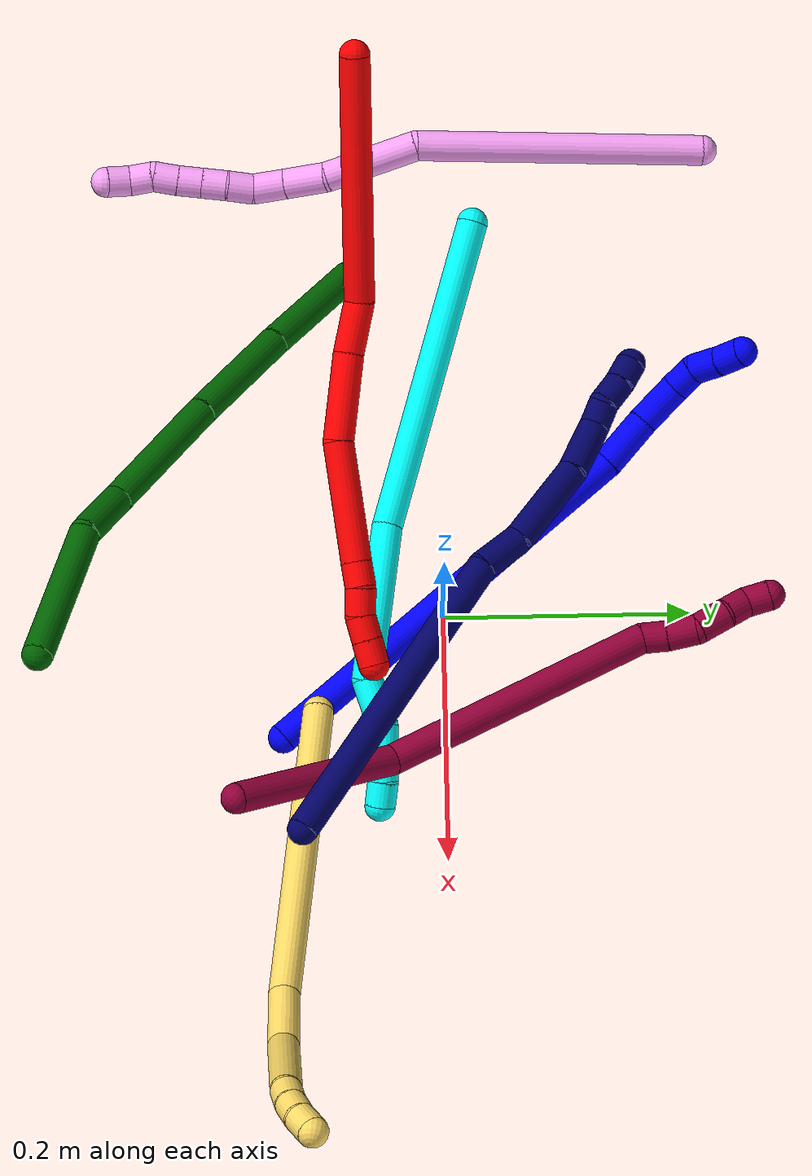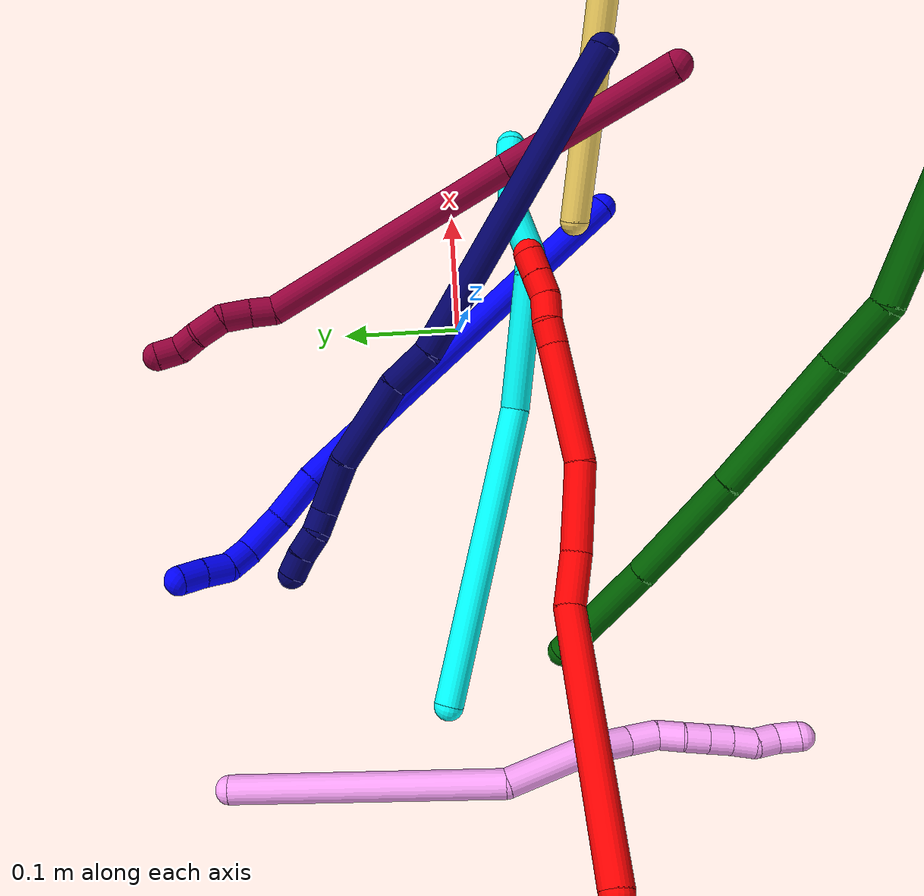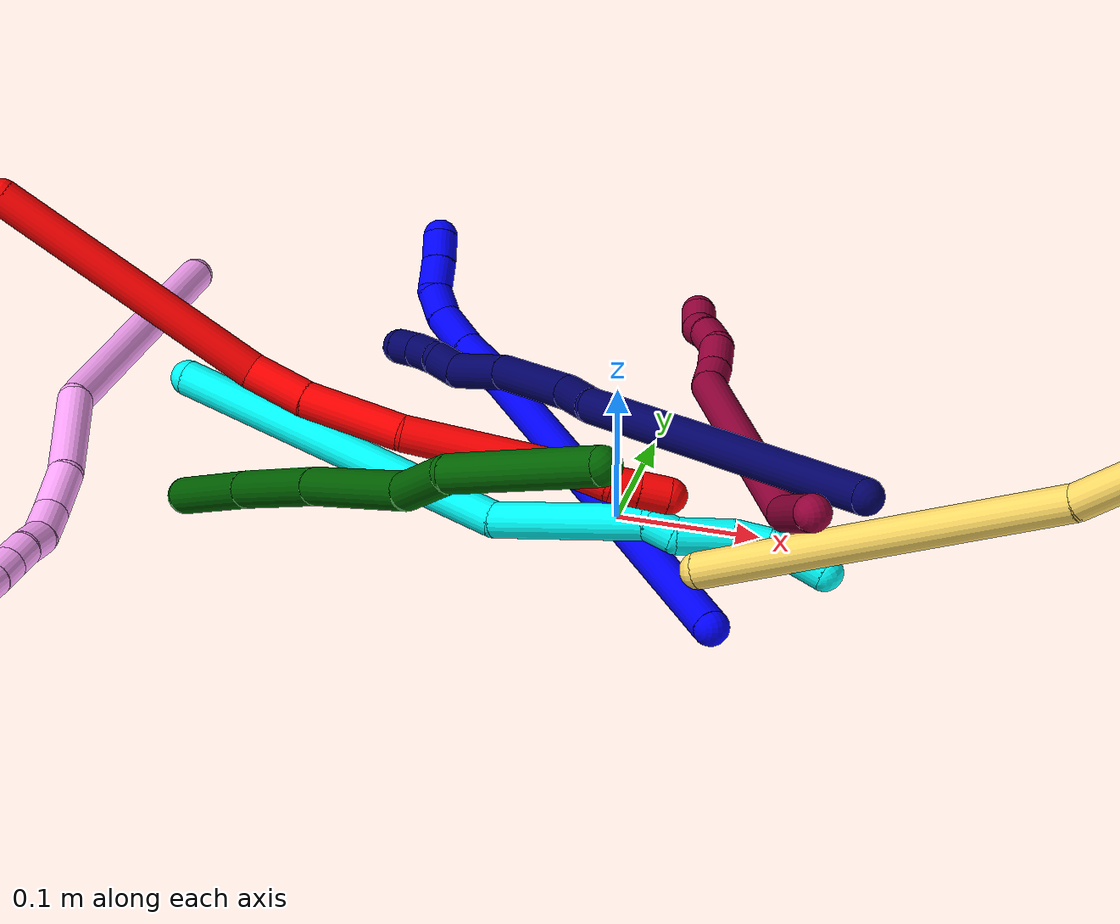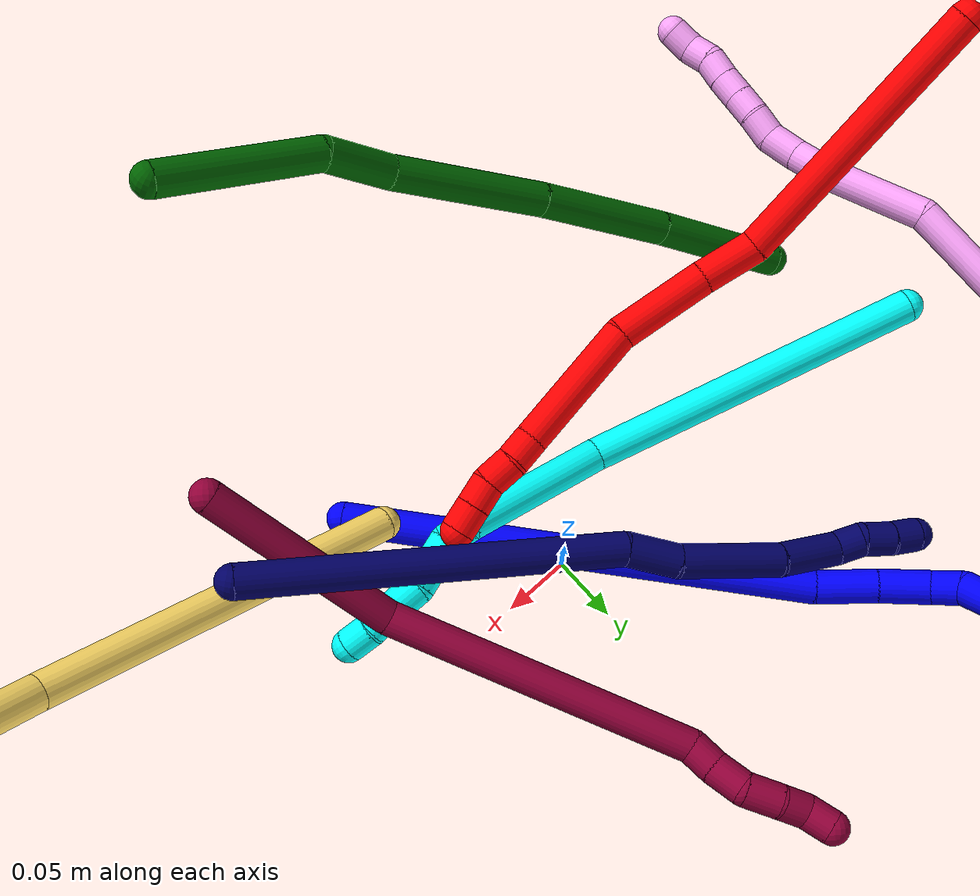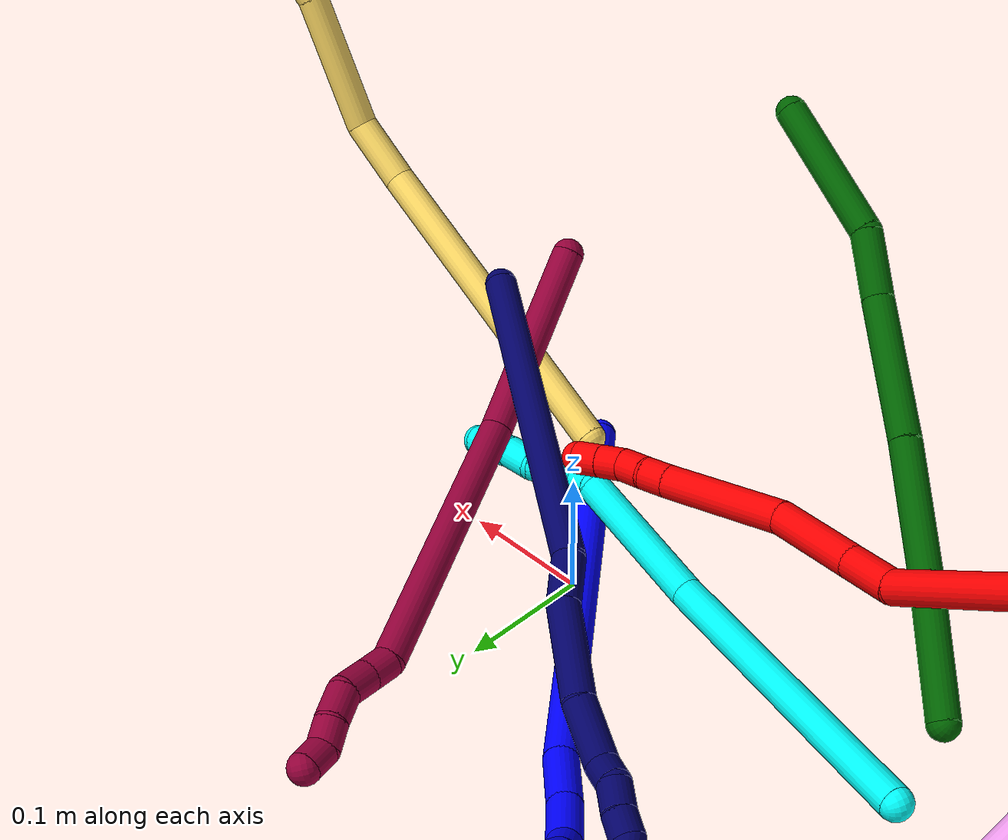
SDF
<sdf version="1.7">
 <world name="default">
  <plugin name="TubeGeneratorPlugin" filename="libtube_generator_plugin.so"/>
  <model name="photoneo_s_sensor">
   <static>1</static>
   <pose>0 0 2 1.57079 1.57079 3.14159</pose>
   <link name="link">
    <inertial><mass>0.1</mass></inertial>
    <sensor name="sensor" type="depth">
     <update_rate>30</update_rate>
     <camera>
      <horizontal_fov>1.22</horizontal_fov>
      <image><width>1920</width><height>1200</height><format>B8G8R8</format></image>
      <clip><near>0.1</near><far>4</far></clip>
      <depth_camera><output>points</output></depth_camera>
     </camera>
     <plugin name="camera_plugin" filename="libgazebo_ros_depth_camera.so">
      <baseline>0.2</baseline>
      <alwaysOn>1</alwaysOn>
      <updateRate>0.0</updateRate>
      <cameraName>camera_ir</cameraName>
      <imageTopicName>/camera/color/image_raw</imageTopicName>
      <cameraInfoTopicName>/camera/color/camera_info</cameraInfoTopicName>
      <depthImageTopicName>/camera/depth/image_raw</depthImageTopicName>
      <depthImageCameraInfoTopicName>/camera/depth/camera_info</depthImageCameraInfoTopicName>
      <pointCloudTopicName>/camera/depth/points</pointCloudTopicName>
      <frameName>fr_optical</frameName>
      <pointCloudCutoff>0.1</pointCloudCutoff>
      <pointCloudCutoffMax>2.0</pointCloudCutoffMax>
      <distortionK1>0</distortionK1>
      <distortionK2>0</distortionK2>
      <distortionK3>0</distortionK3>
      <distortionT1>0</distortionT1>
      <distortionT2>0</distortionT2>
      <CxPrime>0</CxPrime>
      <Cx>0</Cx>
      <Cy>0</Cy>
      <focalLength>0</focalLength>
      <hackBaseline>0</hackBaseline>
     </plugin>
    </sensor>
   </link>
  </model>
  <gravity>0 0 -9.8</gravity>
  <magnetic_field>6e-06 2.3e-05 -4.2e-05</magnetic_field>
  <atmosphere type="adiabatic"/>
  <physics name="default_physics" default="0" type="ode">
   <max_step_size>0.003</max_step_size>
   <real_time_factor>1</real_time_factor>
   <real_time_update_rate>1000</real_time_update_rate>
   <max_contacts>10000</max_contacts>
   <ode>
    <solver>
     <type>quick</type>
     <iters>100</iters>
     <sor>1.3</sor>
     <use_dynamic_moi_rescaling>0</use_dynamic_moi_rescaling>
    </solver>
    <constraints>
     <contact_max_correcting_vel>0</contact_max_correcting_vel>
     <contact_surface_layer>0.001</contact_surface_layer>
     <cfm>0</cfm>
     <erp>0.2</erp>
    </constraints>
   </ode>
  </physics>
  <scene><ambient>0.4 0.4 0.4 1</ambient><background>0.7 0.7 0.7 1</background><shadows>0</shadows></scene>
  <audio><device>default</device></audio>
  <spherical_coordinates>
   <surface_model>EARTH_WGS84</surface_model>
   <latitude_deg>0</latitude_deg>
   <longitude_deg>0</longitude_deg>
   <elevation>0</elevation>
   <heading_deg>0</heading_deg>
  </spherical_coordinates>
  <model name="bin">
   <static>1</static>
   <link name="bottom">
    <collision name="collision-bottom">
     <pose>0 0 -0.01 0 -0 0</pose>
     <geometry><box><size>0.8 0.6 0.02</size></box></geometry>
     <surface>
      <friction><ode><mu>100</mu><mu2>100</mu2></ode></friction>
      <contact><collide_bitmask>65535</collide_bitmask></contact>
     </surface>
    </collision>
   </link>
   <link name="west_wall">
    <collision name="collision-west_wall">
     <pose>-0.41 0 0.1 0 -0 0</pose>
     <geometry><box><size>0.02 0.6 0.2</size></box></geometry>
     <surface>
      <friction><ode><mu>100</mu><mu2>100</mu2></ode></friction>
      <contact><collide_bitmask>65535</collide_bitmask></contact>
     </surface>
    </collision>
   </link>
   <link name="east_wall">
    <collision name="collision-east_wall">
     <pose>0.41 0 0.1 0 -0 0</pose>
     <geometry><box><size>0.02 0.6 0.2</size></box></geometry>
     <surface>
      <friction><ode><mu>100</mu><mu2>100</mu2></ode></friction>
      <contact><collide_bitmask>65535</collide_bitmask></contact>
     </surface>
    </collision>
   </link>
   <link name="south_wall">
    <collision name="collision-south_wall">
     <pose>0 -0.31 0.1 0 -0 0</pose>
     <geometry><box><size>0.8 0.02 0.2</size></box></geometry>
     <surface>
      <friction><ode><mu>100</mu><mu2>100</mu2></ode></friction>
      <contact><collide_bitmask>65535</collide_bitmask></contact>
     </surface>
    </collision>
   </link>
   <link name="north_wall">
    <collision name="collision-north_wall">
     <pose>0 0.31 0.1 0 -0 0</pose>
     <geometry><box><size>0.8 0.02 0.2</size></box></geometry>
     <surface>
      <friction><ode><mu>100</mu><mu2>100</mu2></ode></friction>
      <contact><collide_bitmask>65535</collide_bitmask></contact>
     </surface>
    </collision>
   </link>
  </model>
  <model name="1">
   <static>0</static>
   <link name="1">
    <collision name="collision-cylinder-e_1_1_4">
     <pose>-0.109023 0.129871 -0.038908 -1.86187 -0.677269 0.883929</pose>
     <geometry><cylinder><radius>0.0125</radius><length>0.347944</length></cylinder></geometry>
     <surface>
      <friction><ode><mu>1.16</mu><mu2>1.16</mu2><slip1>0</slip1><slip2>0</slip2></ode></friction>
      <contact><ode><kp>1e+06</kp><kd>1</kd><max_vel>0</max_vel><min_depth>0.001</min_depth></ode></contact>
     </surface>
    </collision>
    <visual name="visual-cylinder-e_1_1_4">
     <pose>-0.109023 0.129871 -0.038908 -1.86187 -0.677269 0.883929</pose>
     <geometry><cylinder><radius>0.0125</radius><length>0.347944</length></cylinder></geometry>
     <material><ambient>0 0 1 1</ambient></material>
    </visual>
    <collision name="collision-cylinder-e_2_4_5">
     <pose>-0.231378 0.277703 -0.079168 -1.64597 -0.637245 0.683378</pose>
     <geometry><cylinder><radius>0.0125</radius><length>0.044818</length></cylinder></geometry>
     <surface>
      <friction><ode><mu>1.16</mu><mu2>1.16</mu2><slip1>0</slip1><slip2>0</slip2></ode></friction>
      <contact><ode><kp>1e+06</kp><kd>1</kd><max_vel>0</max_vel><min_depth>0.001</min_depth></ode></contact>
     </surface>
    </collision>
    <visual name="visual-cylinder-e_2_4_5">
     <pose>-0.231378 0.277703 -0.079168 -1.64597 -0.637245 0.683378</pose>
     <geometry><cylinder><radius>0.0125</radius><length>0.044818</length></cylinder></geometry>
     <material><ambient>0 0 1 1</ambient></material>
    </visual>
    <collision name="collision-cylinder-e_3_5_6">
     <pose>-0.254892 0.311886 -0.082665 -1.70216 -0.556522 0.630089</pose>
     <geometry><cylinder><radius>0.0125</radius><length>0.038546</length></cylinder></geometry>
     <surface>
      <friction><ode><mu>1.16</mu><mu2>1.16</mu2><slip1>0</slip1><slip2>0</slip2></ode></friction>
      <contact><ode><kp>1e+06</kp><kd>1</kd><max_vel>0</max_vel><min_depth>0.001</min_depth></ode></contact>
     </surface>
    </collision>
    <visual name="visual-cylinder-e_3_5_6">
     <pose>-0.254892 0.311886 -0.082665 -1.70216 -0.556522 0.630089</pose>
     <geometry><cylinder><radius>0.0125</radius><length>0.038546</length></cylinder></geometry>
     <material><ambient>0 0 1 1</ambient></material>
    </visual>
    <collision name="collision-cylinder-e_4_6_7">
     <pose>-0.266626 0.339495 -0.086035 -1.67813 -0.134834 0.150088</pose>
     <geometry><cylinder><radius>0.0125</radius><length>0.023112</length></cylinder></geometry>
     <surface>
      <friction><ode><mu>1.16</mu><mu2>1.16</mu2><slip1>0</slip1><slip2>0</slip2></ode></friction>
      <contact><ode><kp>1e+06</kp><kd>1</kd><max_vel>0</max_vel><min_depth>0.001</min_depth></ode></contact>
     </surface>
    </collision>
    <visual name="visual-cylinder-e_4_6_7">
     <pose>-0.266626 0.339495 -0.086035 -1.67813 -0.134834 0.150088</pose>
     <geometry><cylinder><radius>0.0125</radius><length>0.023112</length></cylinder></geometry>
     <material><ambient>0 0 1 1</ambient></material>
    </visual>
    <collision name="collision-cylinder-e_5_7_8">
     <pose>-0.26736 0.361372 -0.09286 -2.06099 0.068772 -0.11457</pose>
     <geometry><cylinder><radius>0.0125</radius><length>0.02384</length></cylinder></geometry>
     <surface>
      <friction><ode><mu>1.16</mu><mu2>1.16</mu2><slip1>0</slip1><slip2>0</slip2></ode></friction>
      <contact><ode><kp>1e+06</kp><kd>1</kd><max_vel>0</max_vel><min_depth>0.001</min_depth></ode></contact>
     </surface>
    </collision>
    <visual name="visual-cylinder-e_5_7_8">
     <pose>-0.26736 0.361372 -0.09286 -2.06099 0.068772 -0.11457</pose>
     <geometry><cylinder><radius>0.0125</radius><length>0.02384</length></cylinder></geometry>
     <material><ambient>0 0 1 1</ambient></material>
    </visual>
    <collision name="collision-cylinder-e_6_8_2">
     <pose>-0.265977 0.381813 -0.102801 -1.98228 0.051924 -0.079289</pose>
     <geometry><cylinder><radius>0.0125</radius><length>0.02174</length></cylinder></geometry>
     <surface>
      <friction><ode><mu>1.16</mu><mu2>1.16</mu2><slip1>0</slip1><slip2>0</slip2></ode></friction>
      <contact><ode><kp>1e+06</kp><kd>1</kd><max_vel>0</max_vel><min_depth>0.001</min_depth></ode></contact>
     </surface>
    </collision>
    <visual name="visual-cylinder-e_6_8_2">
     <pose>-0.265977 0.381813 -0.102801 -1.98228 0.051924 -0.079289</pose>
     <geometry><cylinder><radius>0.0125</radius><length>0.02174</length></cylinder></geometry>
     <material><ambient>0 0 1 1</ambient></material>
    </visual>
    <collision name="collision-sphere-2">
     <pose>-0.265413 0.391762 -0.107143 0 -0 0</pose>
     <geometry><sphere><radius>0.0125</radius></sphere></geometry>
     <surface>
      <friction><ode><mu>1.16</mu><mu2>1.16</mu2><slip1>0</slip1><slip2>0</slip2></ode></friction>
      <contact><ode><kp>1e+06</kp><kd>1</kd><max_vel>0</max_vel><min_depth>0.001</min_depth></ode></contact>
     </surface>
    </collision>
    <visual name="visual-sphere-2">
     <pose>-0.265413 0.391762 -0.107143 0 -0 0</pose>
     <geometry><sphere><radius>0.0125</radius></sphere></geometry>
     <material><ambient>0 0 1 1</ambient></material>
    </visual>
    <collision name="collision-sphere-4">
     <pose>-0.218045 0.259743 -0.077816 0 -0 0</pose>
     <geometry><sphere><radius>0.0125</radius></sphere></geometry>
     <surface>
      <friction><ode><mu>1.16</mu><mu2>1.16</mu2><slip1>0</slip1><slip2>0</slip2></ode></friction>
      <contact><ode><kp>1e+06</kp><kd>1</kd><max_vel>0</max_vel><min_depth>0.001</min_depth></ode></contact>
     </surface>
    </collision>
    <visual name="visual-sphere-4">
     <pose>-0.218045 0.259743 -0.077816 0 -0 0</pose>
     <geometry><sphere><radius>0.0125</radius></sphere></geometry>
     <material><ambient>0 0 1 1</ambient></material>
    </visual>
    <collision name="collision-sphere-1">
     <geometry><sphere><radius>0.0125</radius></sphere></geometry>
     <surface>
      <friction><ode><mu>1.16</mu><mu2>1.16</mu2><slip1>0</slip1><slip2>0</slip2></ode></friction>
      <contact><ode><kp>1e+06</kp><kd>1</kd><max_vel>0</max_vel><min_depth>0.001</min_depth></ode></contact>
     </surface>
    </collision>
    <visual name="visual-sphere-1">
     <geometry><sphere><radius>0.0125</radius></sphere></geometry>
     <material><ambient>0 0 1 1</ambient></material>
    </visual>
    <collision name="collision-sphere-8">
     <pose>-0.266541 0.371863 -0.098459 0 -0 0</pose>
     <geometry><sphere><radius>0.0125</radius></sphere></geometry>
     <surface>
      <friction><ode><mu>1.16</mu><mu2>1.16</mu2><slip1>0</slip1><slip2>0</slip2></ode></friction>
      <contact><ode><kp>1e+06</kp><kd>1</kd><max_vel>0</max_vel><min_depth>0.001</min_depth></ode></contact>
     </surface>
    </collision>
    <visual name="visual-sphere-8">
     <pose>-0.266541 0.371863 -0.098459 0 -0 0</pose>
     <geometry><sphere><radius>0.0125</radius></sphere></geometry>
     <material><ambient>0 0 1 1</ambient></material>
    </visual>
    <collision name="collision-sphere-5">
     <pose>-0.244711 0.295663 -0.080521 0 -0 0</pose>
     <geometry><sphere><radius>0.0125</radius></sphere></geometry>
     <surface>
      <friction><ode><mu>1.16</mu><mu2>1.16</mu2><slip1>0</slip1><slip2>0</slip2></ode></friction>
      <contact><ode><kp>1e+06</kp><kd>1</kd><max_vel>0</max_vel><min_depth>0.001</min_depth></ode></contact>
     </surface>
    </collision>
    <visual name="visual-sphere-5">
     <pose>-0.244711 0.295663 -0.080521 0 -0 0</pose>
     <geometry><sphere><radius>0.0125</radius></sphere></geometry>
     <material><ambient>0 0 1 1</ambient></material>
    </visual>
    <collision name="collision-sphere-6">
     <pose>-0.265072 0.32811 -0.084808 0 -0 0</pose>
     <geometry><sphere><radius>0.0125</radius></sphere></geometry>
     <surface>
      <friction><ode><mu>1.16</mu><mu2>1.16</mu2><slip1>0</slip1><slip2>0</slip2></ode></friction>
      <contact><ode><kp>1e+06</kp><kd>1</kd><max_vel>0</max_vel><min_depth>0.001</min_depth></ode></contact>
     </surface>
    </collision>
    <visual name="visual-sphere-6">
     <pose>-0.265072 0.32811 -0.084808 0 -0 0</pose>
     <geometry><sphere><radius>0.0125</radius></sphere></geometry>
     <material><ambient>0 0 1 1</ambient></material>
    </visual>
    <collision name="collision-sphere-7">
     <pose>-0.268179 0.35088 -0.087262 0 -0 0</pose>
     <geometry><sphere><radius>0.0125</radius></sphere></geometry>
     <surface>
      <friction><ode><mu>1.16</mu><mu2>1.16</mu2><slip1>0</slip1><slip2>0</slip2></ode></friction>
      <contact><ode><kp>1e+06</kp><kd>1</kd><max_vel>0</max_vel><min_depth>0.001</min_depth></ode></contact>
     </surface>
    </collision>
    <visual name="visual-sphere-7">
     <pose>-0.268179 0.35088 -0.087262 0 -0 0</pose>
     <geometry><sphere><radius>0.0125</radius></sphere></geometry>
     <material><ambient>0 0 1 1</ambient></material>
    </visual>
    <inertial>
     <pose>-0.152894 0.188836 -0.053419 0 -0 0</pose>
     <mass>0.5</mass>
     <inertia>
      <ixx>0.003868</ixx>
      <ixy>0</ixy>
      <ixz>0</ixz>
      <iyy>0.003159</iyy>
      <iyz>0</iyz>
      <izz>-0.00044</izz>
     </inertia>
    </inertial>
   </link>
   <pose>0.099062 -0.130935 0.011493 1.2571 -0.796751 -0.416354</pose>
  </model>
  <model name="2">
   <static>0</static>
   <link name="2">
    <collision name="collision-cylinder-e_1_1_4">
     <pose>0.002071 0.029109 -0.097416 -2.85123 0.020362 -0.139044</pose>
     <geometry><cylinder><radius>0.0125</radius><length>0.203386</length></cylinder></geometry>
     <surface>
      <friction><ode><mu>1.16</mu><mu2>1.16</mu2><slip1>0</slip1><slip2>0</slip2></ode></friction>
      <contact><ode><kp>1e+06</kp><kd>1</kd><max_vel>0</max_vel><min_depth>0.001</min_depth></ode></contact>
     </surface>
    </collision>
    <visual name="visual-cylinder-e_1_1_4">
     <pose>0.002071 0.029109 -0.097416 -2.85123 0.020362 -0.139044</pose>
     <geometry><cylinder><radius>0.0125</radius><length>0.203386</length></cylinder></geometry>
     <material><ambient>1 0 0 1</ambient></material>
    </visual>
    <collision name="collision-cylinder-e_2_4_5">
     <pose>0.001242 0.056971 -0.216196 3.0833 -0.134659 -2.32543</pose>
     <geometry><cylinder><radius>0.0125</radius><length>0.043192</length></cylinder></geometry>
     <surface>
      <friction><ode><mu>1.16</mu><mu2>1.16</mu2><slip1>0</slip1><slip2>0</slip2></ode></friction>
      <contact><ode><kp>1e+06</kp><kd>1</kd><max_vel>0</max_vel><min_depth>0.001</min_depth></ode></contact>
     </surface>
    </collision>
    <visual name="visual-cylinder-e_2_4_5">
     <pose>0.001242 0.056971 -0.216196 3.0833 -0.134659 -2.32543</pose>
     <geometry><cylinder><radius>0.0125</radius><length>0.043192</length></cylinder></geometry>
     <material><ambient>1 0 0 1</ambient></material>
    </visual>
    <collision name="collision-cylinder-e_3_5_6">
     <pose>-0.002599 0.050371 -0.272838 2.99101 -0.026366 -0.346064</pose>
     <geometry><cylinder><radius>0.0125</radius><length>0.071389</length></cylinder></geometry>
     <surface>
      <friction><ode><mu>1.16</mu><mu2>1.16</mu2><slip1>0</slip1><slip2>0</slip2></ode></friction>
      <contact><ode><kp>1e+06</kp><kd>1</kd><max_vel>0</max_vel><min_depth>0.001</min_depth></ode></contact>
     </surface>
    </collision>
    <visual name="visual-cylinder-e_3_5_6">
     <pose>-0.002599 0.050371 -0.272838 2.99101 -0.026366 -0.346064</pose>
     <geometry><cylinder><radius>0.0125</radius><length>0.071389</length></cylinder></geometry>
     <material><ambient>1 0 0 1</ambient></material>
    </visual>
    <collision name="collision-cylinder-e_4_6_7">
     <pose>0.007319 0.042237 -0.355905 3.08344 0.223071 2.63348</pose>
     <geometry><cylinder><radius>0.0125</radius><length>0.098171</length></cylinder></geometry>
     <surface>
      <friction><ode><mu>1.16</mu><mu2>1.16</mu2><slip1>0</slip1><slip2>0</slip2></ode></friction>
      <contact><ode><kp>1e+06</kp><kd>1</kd><max_vel>0</max_vel><min_depth>0.001</min_depth></ode></contact>
     </surface>
    </collision>
    <visual name="visual-cylinder-e_4_6_7">
     <pose>0.007319 0.042237 -0.355905 3.08344 0.223071 2.63348</pose>
     <geometry><cylinder><radius>0.0125</radius><length>0.098171</length></cylinder></geometry>
     <material><ambient>1 0 0 1</ambient></material>
    </visual>
    <collision name="collision-cylinder-e_5_7_8">
     <pose>0.020771 0.038281 -0.41366 3.02443 0.252845 2.27695</pose>
     <geometry><cylinder><radius>0.0125</radius><length>0.020731</length></cylinder></geometry>
     <surface>
      <friction><ode><mu>1.16</mu><mu2>1.16</mu2><slip1>0</slip1><slip2>0</slip2></ode></friction>
      <contact><ode><kp>1e+06</kp><kd>1</kd><max_vel>0</max_vel><min_depth>0.001</min_depth></ode></contact>
     </surface>
    </collision>
    <visual name="visual-cylinder-e_5_7_8">
     <pose>0.020771 0.038281 -0.41366 3.02443 0.252845 2.27695</pose>
     <geometry><cylinder><radius>0.0125</radius><length>0.020731</length></cylinder></geometry>
     <material><ambient>1 0 0 1</ambient></material>
    </visual>
    <collision name="collision-cylinder-e_6_8_9">
     <pose>0.023921 0.036934 -0.434829 3.12602 0.049661 2.53407</pose>
     <geometry><cylinder><radius>0.0125</radius><length>0.022433</length></cylinder></geometry>
     <surface>
      <friction><ode><mu>1.16</mu><mu2>1.16</mu2><slip1>0</slip1><slip2>0</slip2></ode></friction>
      <contact><ode><kp>1e+06</kp><kd>1</kd><max_vel>0</max_vel><min_depth>0.001</min_depth></ode></contact>
     </surface>
    </collision>
    <visual name="visual-cylinder-e_6_8_9">
     <pose>0.023921 0.036934 -0.434829 3.12602 0.049661 2.53407</pose>
     <geometry><cylinder><radius>0.0125</radius><length>0.022433</length></cylinder></geometry>
     <material><ambient>1 0 0 1</ambient></material>
    </visual>
    <collision name="collision-cylinder-e_7_9_10">
     <pose>0.027798 0.037009 -0.455509 -3.11526 0.336842 -2.98704</pose>
     <geometry><cylinder><radius>0.0125</radius><length>0.020094</length></cylinder></geometry>
     <surface>
      <friction><ode><mu>1.16</mu><mu2>1.16</mu2><slip1>0</slip1><slip2>0</slip2></ode></friction>
      <contact><ode><kp>1e+06</kp><kd>1</kd><max_vel>0</max_vel><min_depth>0.001</min_depth></ode></contact>
     </surface>
    </collision>
    <visual name="visual-cylinder-e_7_9_10">
     <pose>0.027798 0.037009 -0.455509 -3.11526 0.336842 -2.98704</pose>
     <geometry><cylinder><radius>0.0125</radius><length>0.020094</length></cylinder></geometry>
     <material><ambient>1 0 0 1</ambient></material>
    </visual>
    <collision name="collision-cylinder-e_8_10_2">
     <pose>0.034478 0.037571 -0.474722 -3.10948 0.332156 -2.95061</pose>
     <geometry><cylinder><radius>0.0125</radius><length>0.020604</length></cylinder></geometry>
     <surface>
      <friction><ode><mu>1.16</mu><mu2>1.16</mu2><slip1>0</slip1><slip2>0</slip2></ode></friction>
      <contact><ode><kp>1e+06</kp><kd>1</kd><max_vel>0</max_vel><min_depth>0.001</min_depth></ode></contact>
     </surface>
    </collision>
    <visual name="visual-cylinder-e_8_10_2">
     <pose>0.034478 0.037571 -0.474722 -3.10948 0.332156 -2.95061</pose>
     <geometry><cylinder><radius>0.0125</radius><length>0.020604</length></cylinder></geometry>
     <material><ambient>1 0 0 1</ambient></material>
    </visual>
    <collision name="collision-sphere-2">
     <pose>0.037838 0.037884 -0.484456 0 -0 0</pose>
     <geometry><sphere><radius>0.0125</radius></sphere></geometry>
     <surface>
      <friction><ode><mu>1.16</mu><mu2>1.16</mu2><slip1>0</slip1><slip2>0</slip2></ode></friction>
      <contact><ode><kp>1e+06</kp><kd>1</kd><max_vel>0</max_vel><min_depth>0.001</min_depth></ode></contact>
     </surface>
    </collision>
    <visual name="visual-sphere-2">
     <pose>0.037838 0.037884 -0.484456 0 -0 0</pose>
     <geometry><sphere><radius>0.0125</radius></sphere></geometry>
     <material><ambient>1 0 0 1</ambient></material>
    </visual>
    <collision name="collision-sphere-10">
     <pose>0.031119 0.037259 -0.464989 0 -0 0</pose>
     <geometry><sphere><radius>0.0125</radius></sphere></geometry>
     <surface>
      <friction><ode><mu>1.16</mu><mu2>1.16</mu2><slip1>0</slip1><slip2>0</slip2></ode></friction>
      <contact><ode><kp>1e+06</kp><kd>1</kd><max_vel>0</max_vel><min_depth>0.001</min_depth></ode></contact>
     </surface>
    </collision>
    <visual name="visual-sphere-10">
     <pose>0.031119 0.037259 -0.464989 0 -0 0</pose>
     <geometry><sphere><radius>0.0125</radius></sphere></geometry>
     <material><ambient>1 0 0 1</ambient></material>
    </visual>
    <collision name="collision-sphere-9">
     <pose>0.024478 0.036759 -0.44603 0 -0 0</pose>
     <geometry><sphere><radius>0.0125</radius></sphere></geometry>
     <surface>
      <friction><ode><mu>1.16</mu><mu2>1.16</mu2><slip1>0</slip1><slip2>0</slip2></ode></friction>
      <contact><ode><kp>1e+06</kp><kd>1</kd><max_vel>0</max_vel><min_depth>0.001</min_depth></ode></contact>
     </surface>
    </collision>
    <visual name="visual-sphere-9">
     <pose>0.024478 0.036759 -0.44603 0 -0 0</pose>
     <geometry><sphere><radius>0.0125</radius></sphere></geometry>
     <material><ambient>1 0 0 1</ambient></material>
    </visual>
    <collision name="collision-sphere-4">
     <pose>0.004141 0.058217 -0.194831 0 -0 0</pose>
     <geometry><sphere><radius>0.0125</radius></sphere></geometry>
     <surface>
      <friction><ode><mu>1.16</mu><mu2>1.16</mu2><slip1>0</slip1><slip2>0</slip2></ode></friction>
      <contact><ode><kp>1e+06</kp><kd>1</kd><max_vel>0</max_vel><min_depth>0.001</min_depth></ode></contact>
     </surface>
    </collision>
    <visual name="visual-sphere-4">
     <pose>0.004141 0.058217 -0.194831 0 -0 0</pose>
     <geometry><sphere><radius>0.0125</radius></sphere></geometry>
     <material><ambient>1 0 0 1</ambient></material>
    </visual>
    <collision name="collision-sphere-1">
     <geometry><sphere><radius>0.0125</radius></sphere></geometry>
     <surface>
      <friction><ode><mu>1.16</mu><mu2>1.16</mu2><slip1>0</slip1><slip2>0</slip2></ode></friction>
      <contact><ode><kp>1e+06</kp><kd>1</kd><max_vel>0</max_vel><min_depth>0.001</min_depth></ode></contact>
     </surface>
    </collision>
    <visual name="visual-sphere-1">
     <geometry><sphere><radius>0.0125</radius></sphere></geometry>
     <material><ambient>1 0 0 1</ambient></material>
    </visual>
    <collision name="collision-sphere-8">
     <pose>0.023364 0.037108 -0.423627 0 -0 0</pose>
     <geometry><sphere><radius>0.0125</radius></sphere></geometry>
     <surface>
      <friction><ode><mu>1.16</mu><mu2>1.16</mu2><slip1>0</slip1><slip2>0</slip2></ode></friction>
      <contact><ode><kp>1e+06</kp><kd>1</kd><max_vel>0</max_vel><min_depth>0.001</min_depth></ode></contact>
     </surface>
    </collision>
    <visual name="visual-sphere-8">
     <pose>0.023364 0.037108 -0.423627 0 -0 0</pose>
     <geometry><sphere><radius>0.0125</radius></sphere></geometry>
     <material><ambient>1 0 0 1</ambient></material>
    </visual>
    <collision name="collision-sphere-5">
     <pose>-0.001658 0.055724 -0.23756 0 -0 0</pose>
     <geometry><sphere><radius>0.0125</radius></sphere></geometry>
     <surface>
      <friction><ode><mu>1.16</mu><mu2>1.16</mu2><slip1>0</slip1><slip2>0</slip2></ode></friction>
      <contact><ode><kp>1e+06</kp><kd>1</kd><max_vel>0</max_vel><min_depth>0.001</min_depth></ode></contact>
     </surface>
    </collision>
    <visual name="visual-sphere-5">
     <pose>-0.001658 0.055724 -0.23756 0 -0 0</pose>
     <geometry><sphere><radius>0.0125</radius></sphere></geometry>
     <material><ambient>1 0 0 1</ambient></material>
    </visual>
    <collision name="collision-sphere-6">
     <pose>-0.00354 0.045019 -0.308117 0 -0 0</pose>
     <geometry><sphere><radius>0.0125</radius></sphere></geometry>
     <surface>
      <friction><ode><mu>1.16</mu><mu2>1.16</mu2><slip1>0</slip1><slip2>0</slip2></ode></friction>
      <contact><ode><kp>1e+06</kp><kd>1</kd><max_vel>0</max_vel><min_depth>0.001</min_depth></ode></contact>
     </surface>
    </collision>
    <visual name="visual-sphere-6">
     <pose>-0.00354 0.045019 -0.308117 0 -0 0</pose>
     <geometry><sphere><radius>0.0125</radius></sphere></geometry>
     <material><ambient>1 0 0 1</ambient></material>
    </visual>
    <collision name="collision-sphere-7">
     <pose>0.018178 0.039455 -0.403693 0 -0 0</pose>
     <geometry><sphere><radius>0.0125</radius></sphere></geometry>
     <surface>
      <friction><ode><mu>1.16</mu><mu2>1.16</mu2><slip1>0</slip1><slip2>0</slip2></ode></friction>
      <contact><ode><kp>1e+06</kp><kd>1</kd><max_vel>0</max_vel><min_depth>0.001</min_depth></ode></contact>
     </surface>
    </collision>
    <visual name="visual-sphere-7">
     <pose>0.018178 0.039455 -0.403693 0 -0 0</pose>
     <geometry><sphere><radius>0.0125</radius></sphere></geometry>
     <material><ambient>1 0 0 1</ambient></material>
    </visual>
    <inertial>
     <pose>0.006488 0.038527 -0.241665 0 -0 0</pose>
     <mass>0.5</mass>
     <inertia>
      <ixx>0.00058</ixx>
      <ixy>0</ixy>
      <ixz>0</ixz>
      <iyy>-0.000691</iyy>
      <iyz>0</iyz>
      <izz>-0.000263</izz>
     </inertia>
    </inertial>
   </link>
   <pose>-0.40949 -0.06285 0.21949 -1.29478 -0.165984 1.44182</pose>
  </model>
  <model name="3">
   <static>0</static>
   <link name="3">
    <collision name="collision-cylinder-e_1_1_4">
     <pose>0.129439 -0.007885 0.00117 1.42351 1.50929 1.36295</pose>
     <geometry><cylinder><radius>0.0125</radius><length>0.259368</length></cylinder></geometry>
     <surface>
      <friction><ode><mu>1.16</mu><mu2>1.16</mu2><slip1>0</slip1><slip2>0</slip2></ode></friction>
      <contact><ode><kp>1e+06</kp><kd>1</kd><max_vel>0</max_vel><min_depth>0.001</min_depth></ode></contact>
     </surface>
    </collision>
    <visual name="visual-cylinder-e_1_1_4">
     <pose>0.129439 -0.007885 0.00117 1.42351 1.50929 1.36295</pose>
     <geometry><cylinder><radius>0.0125</radius><length>0.259368</length></cylinder></geometry>
     <material><ambient>0.003922 1 0.996078 1</ambient></material>
    </visual>
    <collision name="collision-cylinder-e_2_4_5">
     <pose>0.313753 0.000741 -0.005398 -2.00903 1.25 -1.69699</pose>
     <geometry><cylinder><radius>0.0125</radius><length>0.115651</length></cylinder></geometry>
     <surface>
      <friction><ode><mu>1.16</mu><mu2>1.16</mu2><slip1>0</slip1><slip2>0</slip2></ode></friction>
      <contact><ode><kp>1e+06</kp><kd>1</kd><max_vel>0</max_vel><min_depth>0.001</min_depth></ode></contact>
     </surface>
    </collision>
    <visual name="visual-cylinder-e_2_4_5">
     <pose>0.313753 0.000741 -0.005398 -2.00903 1.25 -1.69699</pose>
     <geometry><cylinder><radius>0.0125</radius><length>0.115651</length></cylinder></geometry>
     <material><ambient>0.003922 1 0.996078 1</ambient></material>
    </visual>
    <collision name="collision-cylinder-e_3_5_6">
     <pose>0.378515 0.015105 -0.014428 2.11282 1.32253 1.88532</pose>
     <geometry><cylinder><radius>0.0125</radius><length>0.020398</length></cylinder></geometry>
     <surface>
      <friction><ode><mu>1.16</mu><mu2>1.16</mu2><slip1>0</slip1><slip2>0</slip2></ode></friction>
      <contact><ode><kp>1e+06</kp><kd>1</kd><max_vel>0</max_vel><min_depth>0.001</min_depth></ode></contact>
     </surface>
    </collision>
    <visual name="visual-cylinder-e_3_5_6">
     <pose>0.378515 0.015105 -0.014428 2.11282 1.32253 1.88532</pose>
     <geometry><cylinder><radius>0.0125</radius><length>0.020398</length></cylinder></geometry>
     <material><ambient>0.003922 1 0.996078 1</ambient></material>
    </visual>
    <collision name="collision-cylinder-e_4_6_7">
     <pose>0.404781 0.013081 -0.02664 -3.13027 0.9828 -3.12043</pose>
     <geometry><cylinder><radius>0.0125</radius><length>0.039372</length></cylinder></geometry>
     <surface>
      <friction><ode><mu>1.16</mu><mu2>1.16</mu2><slip1>0</slip1><slip2>0</slip2></ode></friction>
      <contact><ode><kp>1e+06</kp><kd>1</kd><max_vel>0</max_vel><min_depth>0.001</min_depth></ode></contact>
     </surface>
    </collision>
    <visual name="visual-cylinder-e_4_6_7">
     <pose>0.404781 0.013081 -0.02664 -3.13027 0.9828 -3.12043</pose>
     <geometry><cylinder><radius>0.0125</radius><length>0.039372</length></cylinder></geometry>
     <material><ambient>0.003922 1 0.996078 1</ambient></material>
    </visual>
    <collision name="collision-cylinder-e_5_7_8">
     <pose>0.433065 0.012882 -0.040718 3.03957 1.3101 3.00887</pose>
     <geometry><cylinder><radius>0.0125</radius><length>0.024642</length></cylinder></geometry>
     <surface>
      <friction><ode><mu>1.16</mu><mu2>1.16</mu2><slip1>0</slip1><slip2>0</slip2></ode></friction>
      <contact><ode><kp>1e+06</kp><kd>1</kd><max_vel>0</max_vel><min_depth>0.001</min_depth></ode></contact>
     </surface>
    </collision>
    <visual name="visual-cylinder-e_5_7_8">
     <pose>0.433065 0.012882 -0.040718 3.03957 1.3101 3.00887</pose>
     <geometry><cylinder><radius>0.0125</radius><length>0.024642</length></cylinder></geometry>
     <material><ambient>0.003922 1 0.996078 1</ambient></material>
    </visual>
    <collision name="collision-cylinder-e_6_8_9">
     <pose>0.454488 0.010332 -0.046674 2.46925 1.21158 2.20716</pose>
     <geometry><cylinder><radius>0.0125</radius><length>0.020336</length></cylinder></geometry>
     <surface>
      <friction><ode><mu>1.16</mu><mu2>1.16</mu2><slip1>0</slip1><slip2>0</slip2></ode></friction>
      <contact><ode><kp>1e+06</kp><kd>1</kd><max_vel>0</max_vel><min_depth>0.001</min_depth></ode></contact>
     </surface>
    </collision>
    <visual name="visual-cylinder-e_6_8_9">
     <pose>0.454488 0.010332 -0.046674 2.46925 1.21158 2.20716</pose>
     <geometry><cylinder><radius>0.0125</radius><length>0.020336</length></cylinder></geometry>
     <material><ambient>0.003922 1 0.996078 1</ambient></material>
    </visual>
    <collision name="collision-cylinder-e_7_9_2">
     <pose>0.473609 0.005212 -0.050802 2.00205 1.25051 1.68989</pose>
     <geometry><cylinder><radius>0.0125</radius><length>0.020234</length></cylinder></geometry>
     <surface>
      <friction><ode><mu>1.16</mu><mu2>1.16</mu2><slip1>0</slip1><slip2>0</slip2></ode></friction>
      <contact><ode><kp>1e+06</kp><kd>1</kd><max_vel>0</max_vel><min_depth>0.001</min_depth></ode></contact>
     </surface>
    </collision>
    <visual name="visual-cylinder-e_7_9_2">
     <pose>0.473609 0.005212 -0.050802 2.00205 1.25051 1.68989</pose>
     <geometry><cylinder><radius>0.0125</radius><length>0.020234</length></cylinder></geometry>
     <material><ambient>0.003922 1 0.996078 1</ambient></material>
    </visual>
    <collision name="collision-sphere-2">
     <pose>0.483212 0.002319 -0.052133 0 -0 0</pose>
     <geometry><sphere><radius>0.0125</radius></sphere></geometry>
     <surface>
      <friction><ode><mu>1.16</mu><mu2>1.16</mu2><slip1>0</slip1><slip2>0</slip2></ode></friction>
      <contact><ode><kp>1e+06</kp><kd>1</kd><max_vel>0</max_vel><min_depth>0.001</min_depth></ode></contact>
     </surface>
    </collision>
    <visual name="visual-sphere-2">
     <pose>0.483212 0.002319 -0.052133 0 -0 0</pose>
     <geometry><sphere><radius>0.0125</radius></sphere></geometry>
     <material><ambient>0.003922 1 0.996078 1</ambient></material>
    </visual>
    <collision name="collision-sphere-9">
     <pose>0.464007 0.008106 -0.04947 0 -0 0</pose>
     <geometry><sphere><radius>0.0125</radius></sphere></geometry>
     <surface>
      <friction><ode><mu>1.16</mu><mu2>1.16</mu2><slip1>0</slip1><slip2>0</slip2></ode></friction>
      <contact><ode><kp>1e+06</kp><kd>1</kd><max_vel>0</max_vel><min_depth>0.001</min_depth></ode></contact>
     </surface>
    </collision>
    <visual name="visual-sphere-9">
     <pose>0.464007 0.008106 -0.04947 0 -0 0</pose>
     <geometry><sphere><radius>0.0125</radius></sphere></geometry>
     <material><ambient>0.003922 1 0.996078 1</ambient></material>
    </visual>
    <collision name="collision-sphere-4">
     <pose>0.258878 -0.01577 0.00234 0 -0 0</pose>
     <geometry><sphere><radius>0.0125</radius></sphere></geometry>
     <surface>
      <friction><ode><mu>1.16</mu><mu2>1.16</mu2><slip1>0</slip1><slip2>0</slip2></ode></friction>
      <contact><ode><kp>1e+06</kp><kd>1</kd><max_vel>0</max_vel><min_depth>0.001</min_depth></ode></contact>
     </surface>
    </collision>
    <visual name="visual-sphere-4">
     <pose>0.258878 -0.01577 0.00234 0 -0 0</pose>
     <geometry><sphere><radius>0.0125</radius></sphere></geometry>
     <material><ambient>0.003922 1 0.996078 1</ambient></material>
    </visual>
    <collision name="collision-sphere-1">
     <geometry><sphere><radius>0.0125</radius></sphere></geometry>
     <surface>
      <friction><ode><mu>1.16</mu><mu2>1.16</mu2><slip1>0</slip1><slip2>0</slip2></ode></friction>
      <contact><ode><kp>1e+06</kp><kd>1</kd><max_vel>0</max_vel><min_depth>0.001</min_depth></ode></contact>
     </surface>
    </collision>
    <visual name="visual-sphere-1">
     <geometry><sphere><radius>0.0125</radius></sphere></geometry>
     <material><ambient>0.003922 1 0.996078 1</ambient></material>
    </visual>
    <collision name="collision-sphere-8">
     <pose>0.444969 0.012558 -0.043877 0 -0 0</pose>
     <geometry><sphere><radius>0.0125</radius></sphere></geometry>
     <surface>
      <friction><ode><mu>1.16</mu><mu2>1.16</mu2><slip1>0</slip1><slip2>0</slip2></ode></friction>
      <contact><ode><kp>1e+06</kp><kd>1</kd><max_vel>0</max_vel><min_depth>0.001</min_depth></ode></contact>
     </surface>
    </collision>
    <visual name="visual-sphere-8">
     <pose>0.444969 0.012558 -0.043877 0 -0 0</pose>
     <geometry><sphere><radius>0.0125</radius></sphere></geometry>
     <material><ambient>0.003922 1 0.996078 1</ambient></material>
    </visual>
    <collision name="collision-sphere-5">
     <pose>0.368628 0.017252 -0.013135 0 -0 0</pose>
     <geometry><sphere><radius>0.0125</radius></sphere></geometry>
     <surface>
      <friction><ode><mu>1.16</mu><mu2>1.16</mu2><slip1>0</slip1><slip2>0</slip2></ode></friction>
      <contact><ode><kp>1e+06</kp><kd>1</kd><max_vel>0</max_vel><min_depth>0.001</min_depth></ode></contact>
     </surface>
    </collision>
    <visual name="visual-sphere-5">
     <pose>0.368628 0.017252 -0.013135 0 -0 0</pose>
     <geometry><sphere><radius>0.0125</radius></sphere></geometry>
     <material><ambient>0.003922 1 0.996078 1</ambient></material>
    </visual>
    <collision name="collision-sphere-6">
     <pose>0.388401 0.012958 -0.015721 0 -0 0</pose>
     <geometry><sphere><radius>0.0125</radius></sphere></geometry>
     <surface>
      <friction><ode><mu>1.16</mu><mu2>1.16</mu2><slip1>0</slip1><slip2>0</slip2></ode></friction>
      <contact><ode><kp>1e+06</kp><kd>1</kd><max_vel>0</max_vel><min_depth>0.001</min_depth></ode></contact>
     </surface>
    </collision>
    <visual name="visual-sphere-6">
     <pose>0.388401 0.012958 -0.015721 0 -0 0</pose>
     <geometry><sphere><radius>0.0125</radius></sphere></geometry>
     <material><ambient>0.003922 1 0.996078 1</ambient></material>
    </visual>
    <collision name="collision-sphere-7">
     <pose>0.42116 0.013205 -0.037559 0 -0 0</pose>
     <geometry><sphere><radius>0.0125</radius></sphere></geometry>
     <surface>
      <friction><ode><mu>1.16</mu><mu2>1.16</mu2><slip1>0</slip1><slip2>0</slip2></ode></friction>
      <contact><ode><kp>1e+06</kp><kd>1</kd><max_vel>0</max_vel><min_depth>0.001</min_depth></ode></contact>
     </surface>
    </collision>
    <visual name="visual-sphere-7">
     <pose>0.42116 0.013205 -0.037559 0 -0 0</pose>
     <geometry><sphere><radius>0.0125</radius></sphere></geometry>
     <material><ambient>0.003922 1 0.996078 1</ambient></material>
    </visual>
    <inertial>
     <pose>0.246025 -0.001007 -0.009289 0 -0 0</pose>
     <mass>0.5</mass>
     <inertia>
      <ixx>9.4e-05</ixx>
      <ixy>0</ixy>
      <ixz>0</ixz>
      <iyy>0.00164</iyy>
      <iyz>0</iyz>
      <izz>-0.001552</izz>
     </inertia>
    </inertial>
   </link>
   <pose>-0.320561 0.030148 0.041323 1.54774 0.054575 -0.282407</pose>
  </model>
  <model name="4">
   <static>0</static>
   <link name="4">
    <collision name="collision-cylinder-e_1_1_4">
     <pose>0.00044 0.000142 0.118205 -0.001205 0.003721 -2e-06</pose>
     <geometry><cylinder><radius>0.0125</radius><length>0.236411</length></cylinder></geometry>
     <surface>
      <friction><ode><mu>1.16</mu><mu2>1.16</mu2><slip1>0</slip1><slip2>0</slip2></ode></friction>
      <contact><ode><kp>1e+06</kp><kd>1</kd><max_vel>0</max_vel><min_depth>0.001</min_depth></ode></contact>
     </surface>
    </collision>
    <visual name="visual-cylinder-e_1_1_4">
     <pose>0.00044 0.000142 0.118205 -0.001205 0.003721 -2e-06</pose>
     <geometry><cylinder><radius>0.0125</radius><length>0.236411</length></cylinder></geometry>
     <material><ambient>1 0.65098 0.996078 1</ambient></material>
    </visual>
    <collision name="collision-cylinder-e_2_4_5">
     <pose>3.3e-05 -0.01473 0.272411 0.395112 -0.021709 -0.004346</pose>
     <geometry><cylinder><radius>0.0125</radius><length>0.078033</length></cylinder></geometry>
     <surface>
      <friction><ode><mu>1.16</mu><mu2>1.16</mu2><slip1>0</slip1><slip2>0</slip2></ode></friction>
      <contact><ode><kp>1e+06</kp><kd>1</kd><max_vel>0</max_vel><min_depth>0.001</min_depth></ode></contact>
     </surface>
    </collision>
    <visual name="visual-cylinder-e_2_4_5">
     <pose>3.3e-05 -0.01473 0.272411 0.395112 -0.021709 -0.004346</pose>
     <geometry><cylinder><radius>0.0125</radius><length>0.078033</length></cylinder></geometry>
     <material><ambient>1 0.65098 0.996078 1</ambient></material>
    </visual>
    <collision name="collision-cylinder-e_3_5_6">
     <pose>-0.005608 -0.035205 0.324595 0.32549 -0.273632 -0.045204</pose>
     <geometry><cylinder><radius>0.0125</radius><length>0.035477</length></cylinder></geometry>
     <surface>
      <friction><ode><mu>1.16</mu><mu2>1.16</mu2><slip1>0</slip1><slip2>0</slip2></ode></friction>
      <contact><ode><kp>1e+06</kp><kd>1</kd><max_vel>0</max_vel><min_depth>0.001</min_depth></ode></contact>
     </surface>
    </collision>
    <visual name="visual-cylinder-e_3_5_6">
     <pose>-0.005608 -0.035205 0.324595 0.32549 -0.273632 -0.045204</pose>
     <geometry><cylinder><radius>0.0125</radius><length>0.035477</length></cylinder></geometry>
     <material><ambient>1 0.65098 0.996078 1</ambient></material>
    </visual>
    <collision name="collision-cylinder-e_4_6_7">
     <pose>-0.011485 -0.043747 0.35405 0.228029 -0.079338 -0.00909</pose>
     <geometry><cylinder><radius>0.0125</radius><length>0.027338</length></cylinder></geometry>
     <surface>
      <friction><ode><mu>1.16</mu><mu2>1.16</mu2><slip1>0</slip1><slip2>0</slip2></ode></friction>
      <contact><ode><kp>1e+06</kp><kd>1</kd><max_vel>0</max_vel><min_depth>0.001</min_depth></ode></contact>
     </surface>
    </collision>
    <visual name="visual-cylinder-e_4_6_7">
     <pose>-0.011485 -0.043747 0.35405 0.228029 -0.079338 -0.00909</pose>
     <geometry><cylinder><radius>0.0125</radius><length>0.027338</length></cylinder></geometry>
     <material><ambient>1 0.65098 0.996078 1</ambient></material>
    </visual>
    <collision name="collision-cylinder-e_5_7_8">
     <pose>-0.012567 -0.045448 0.378299 -0.124963 0.000114 -7e-06</pose>
     <geometry><cylinder><radius>0.0125</radius><length>0.022124</length></cylinder></geometry>
     <surface>
      <friction><ode><mu>1.16</mu><mu2>1.16</mu2><slip1>0</slip1><slip2>0</slip2></ode></friction>
      <contact><ode><kp>1e+06</kp><kd>1</kd><max_vel>0</max_vel><min_depth>0.001</min_depth></ode></contact>
     </surface>
    </collision>
    <visual name="visual-cylinder-e_5_7_8">
     <pose>-0.012567 -0.045448 0.378299 -0.124963 0.000114 -7e-06</pose>
     <geometry><cylinder><radius>0.0125</radius><length>0.022124</length></cylinder></geometry>
     <material><ambient>1 0.65098 0.996078 1</ambient></material>
    </visual>
    <collision name="collision-cylinder-e_6_8_9">
     <pose>-0.01411 -0.043772 0.399213 -0.029952 -0.15416 0.002313</pose>
     <geometry><cylinder><radius>0.0125</radius><length>0.020125</length></cylinder></geometry>
     <surface>
      <friction><ode><mu>1.16</mu><mu2>1.16</mu2><slip1>0</slip1><slip2>0</slip2></ode></friction>
      <contact><ode><kp>1e+06</kp><kd>1</kd><max_vel>0</max_vel><min_depth>0.001</min_depth></ode></contact>
     </surface>
    </collision>
    <visual name="visual-cylinder-e_6_8_9">
     <pose>-0.01411 -0.043772 0.399213 -0.029952 -0.15416 0.002313</pose>
     <geometry><cylinder><radius>0.0125</radius><length>0.020125</length></cylinder></geometry>
     <material><ambient>1 0.65098 0.996078 1</ambient></material>
    </visual>
    <collision name="collision-cylinder-e_7_9_10">
     <pose>-0.017133 -0.043181 0.419053 -0.029522 -0.148042 0.002189</pose>
     <geometry><cylinder><radius>0.0125</radius><length>0.020029</length></cylinder></geometry>
     <surface>
      <friction><ode><mu>1.16</mu><mu2>1.16</mu2><slip1>0</slip1><slip2>0</slip2></ode></friction>
      <contact><ode><kp>1e+06</kp><kd>1</kd><max_vel>0</max_vel><min_depth>0.001</min_depth></ode></contact>
     </surface>
    </collision>
    <visual name="visual-cylinder-e_7_9_10">
     <pose>-0.017133 -0.043181 0.419053 -0.029522 -0.148042 0.002189</pose>
     <geometry><cylinder><radius>0.0125</radius><length>0.020029</length></cylinder></geometry>
     <material><ambient>1 0.65098 0.996078 1</ambient></material>
    </visual>
    <collision name="collision-cylinder-e_8_10_11">
     <pose>-0.020139 -0.041888 0.438813 -0.101131 -0.153101 0.007763</pose>
     <geometry><cylinder><radius>0.0125</radius><length>0.020056</length></cylinder></geometry>
     <surface>
      <friction><ode><mu>1.16</mu><mu2>1.16</mu2><slip1>0</slip1><slip2>0</slip2></ode></friction>
      <contact><ode><kp>1e+06</kp><kd>1</kd><max_vel>0</max_vel><min_depth>0.001</min_depth></ode></contact>
     </surface>
    </collision>
    <visual name="visual-cylinder-e_8_10_11">
     <pose>-0.020139 -0.041888 0.438813 -0.101131 -0.153101 0.007763</pose>
     <geometry><cylinder><radius>0.0125</radius><length>0.020056</length></cylinder></geometry>
     <material><ambient>1 0.65098 0.996078 1</ambient></material>
    </visual>
    <collision name="collision-cylinder-e_9_11_12">
     <pose>-0.023162 -0.043654 0.458274 0.280514 -0.148369 -0.020985</pose>
     <geometry><cylinder><radius>0.0125</radius><length>0.020206</length></cylinder></geometry>
     <surface>
      <friction><ode><mu>1.16</mu><mu2>1.16</mu2><slip1>0</slip1><slip2>0</slip2></ode></friction>
      <contact><ode><kp>1e+06</kp><kd>1</kd><max_vel>0</max_vel><min_depth>0.001</min_depth></ode></contact>
     </surface>
    </collision>
    <visual name="visual-cylinder-e_9_11_12">
     <pose>-0.023162 -0.043654 0.458274 0.280514 -0.148369 -0.020985</pose>
     <geometry><cylinder><radius>0.0125</radius><length>0.020206</length></cylinder></geometry>
     <material><ambient>1 0.65098 0.996078 1</ambient></material>
    </visual>
    <collision name="collision-cylinder-e_10_12_2">
     <pose>-0.023058 -0.046474 0.477849 0.005359 0.158772 0.000426</pose>
     <geometry><cylinder><radius>0.0125</radius><length>0.020202</length></cylinder></geometry>
     <surface>
      <friction><ode><mu>1.16</mu><mu2>1.16</mu2><slip1>0</slip1><slip2>0</slip2></ode></friction>
      <contact><ode><kp>1e+06</kp><kd>1</kd><max_vel>0</max_vel><min_depth>0.001</min_depth></ode></contact>
     </surface>
    </collision>
    <visual name="visual-cylinder-e_10_12_2">
     <pose>-0.023058 -0.046474 0.477849 0.005359 0.158772 0.000426</pose>
     <geometry><cylinder><radius>0.0125</radius><length>0.020202</length></cylinder></geometry>
     <material><ambient>1 0.65098 0.996078 1</ambient></material>
    </visual>
    <collision name="collision-sphere-2">
     <pose>-0.021461 -0.046527 0.487823 0 -0 0</pose>
     <geometry><sphere><radius>0.0125</radius></sphere></geometry>
     <surface>
      <friction><ode><mu>1.16</mu><mu2>1.16</mu2><slip1>0</slip1><slip2>0</slip2></ode></friction>
      <contact><ode><kp>1e+06</kp><kd>1</kd><max_vel>0</max_vel><min_depth>0.001</min_depth></ode></contact>
     </surface>
    </collision>
    <visual name="visual-sphere-2">
     <pose>-0.021461 -0.046527 0.487823 0 -0 0</pose>
     <geometry><sphere><radius>0.0125</radius></sphere></geometry>
     <material><ambient>1 0.65098 0.996078 1</ambient></material>
    </visual>
    <collision name="collision-sphere-12">
     <pose>-0.024655 -0.04642 0.467875 0 -0 0</pose>
     <geometry><sphere><radius>0.0125</radius></sphere></geometry>
     <surface>
      <friction><ode><mu>1.16</mu><mu2>1.16</mu2><slip1>0</slip1><slip2>0</slip2></ode></friction>
      <contact><ode><kp>1e+06</kp><kd>1</kd><max_vel>0</max_vel><min_depth>0.001</min_depth></ode></contact>
     </surface>
    </collision>
    <visual name="visual-sphere-12">
     <pose>-0.024655 -0.04642 0.467875 0 -0 0</pose>
     <geometry><sphere><radius>0.0125</radius></sphere></geometry>
     <material><ambient>1 0.65098 0.996078 1</ambient></material>
    </visual>
    <collision name="collision-sphere-11">
     <pose>-0.021668 -0.040888 0.448673 0 -0 0</pose>
     <geometry><sphere><radius>0.0125</radius></sphere></geometry>
     <surface>
      <friction><ode><mu>1.16</mu><mu2>1.16</mu2><slip1>0</slip1><slip2>0</slip2></ode></friction>
      <contact><ode><kp>1e+06</kp><kd>1</kd><max_vel>0</max_vel><min_depth>0.001</min_depth></ode></contact>
     </surface>
    </collision>
    <visual name="visual-sphere-11">
     <pose>-0.021668 -0.040888 0.448673 0 -0 0</pose>
     <geometry><sphere><radius>0.0125</radius></sphere></geometry>
     <material><ambient>1 0.65098 0.996078 1</ambient></material>
    </visual>
    <collision name="collision-sphere-10">
     <pose>-0.01861 -0.042889 0.428953 0 -0 0</pose>
     <geometry><sphere><radius>0.0125</radius></sphere></geometry>
     <surface>
      <friction><ode><mu>1.16</mu><mu2>1.16</mu2><slip1>0</slip1><slip2>0</slip2></ode></friction>
      <contact><ode><kp>1e+06</kp><kd>1</kd><max_vel>0</max_vel><min_depth>0.001</min_depth></ode></contact>
     </surface>
    </collision>
    <visual name="visual-sphere-10">
     <pose>-0.01861 -0.042889 0.428953 0 -0 0</pose>
     <geometry><sphere><radius>0.0125</radius></sphere></geometry>
     <material><ambient>1 0.65098 0.996078 1</ambient></material>
    </visual>
    <collision name="collision-sphere-9">
     <pose>-0.015656 -0.043474 0.409152 0 -0 0</pose>
     <geometry><sphere><radius>0.0125</radius></sphere></geometry>
     <surface>
      <friction><ode><mu>1.16</mu><mu2>1.16</mu2><slip1>0</slip1><slip2>0</slip2></ode></friction>
      <contact><ode><kp>1e+06</kp><kd>1</kd><max_vel>0</max_vel><min_depth>0.001</min_depth></ode></contact>
     </surface>
    </collision>
    <visual name="visual-sphere-9">
     <pose>-0.015656 -0.043474 0.409152 0 -0 0</pose>
     <geometry><sphere><radius>0.0125</radius></sphere></geometry>
     <material><ambient>1 0.65098 0.996078 1</ambient></material>
    </visual>
    <collision name="collision-sphere-4">
     <pose>0.00088 0.000285 0.236409 0 -0 0</pose>
     <geometry><sphere><radius>0.0125</radius></sphere></geometry>
     <surface>
      <friction><ode><mu>1.16</mu><mu2>1.16</mu2><slip1>0</slip1><slip2>0</slip2></ode></friction>
      <contact><ode><kp>1e+06</kp><kd>1</kd><max_vel>0</max_vel><min_depth>0.001</min_depth></ode></contact>
     </surface>
    </collision>
    <visual name="visual-sphere-4">
     <pose>0.00088 0.000285 0.236409 0 -0 0</pose>
     <geometry><sphere><radius>0.0125</radius></sphere></geometry>
     <material><ambient>1 0.65098 0.996078 1</ambient></material>
    </visual>
    <collision name="collision-sphere-1">
     <geometry><sphere><radius>0.0125</radius></sphere></geometry>
     <surface>
      <friction><ode><mu>1.16</mu><mu2>1.16</mu2><slip1>0</slip1><slip2>0</slip2></ode></friction>
      <contact><ode><kp>1e+06</kp><kd>1</kd><max_vel>0</max_vel><min_depth>0.001</min_depth></ode></contact>
     </surface>
    </collision>
    <visual name="visual-sphere-1">
     <geometry><sphere><radius>0.0125</radius></sphere></geometry>
     <material><ambient>1 0.65098 0.996078 1</ambient></material>
    </visual>
    <collision name="collision-sphere-8">
     <pose>-0.012565 -0.044069 0.389275 0 -0 0</pose>
     <geometry><sphere><radius>0.0125</radius></sphere></geometry>
     <surface>
      <friction><ode><mu>1.16</mu><mu2>1.16</mu2><slip1>0</slip1><slip2>0</slip2></ode></friction>
      <contact><ode><kp>1e+06</kp><kd>1</kd><max_vel>0</max_vel><min_depth>0.001</min_depth></ode></contact>
     </surface>
    </collision>
    <visual name="visual-sphere-8">
     <pose>-0.012565 -0.044069 0.389275 0 -0 0</pose>
     <geometry><sphere><radius>0.0125</radius></sphere></geometry>
     <material><ambient>1 0.65098 0.996078 1</ambient></material>
    </visual>
    <collision name="collision-sphere-5">
     <pose>-0.000814 -0.029744 0.308413 0 -0 0</pose>
     <geometry><sphere><radius>0.0125</radius></sphere></geometry>
     <surface>
      <friction><ode><mu>1.16</mu><mu2>1.16</mu2><slip1>0</slip1><slip2>0</slip2></ode></friction>
      <contact><ode><kp>1e+06</kp><kd>1</kd><max_vel>0</max_vel><min_depth>0.001</min_depth></ode></contact>
     </surface>
    </collision>
    <visual name="visual-sphere-5">
     <pose>-0.000814 -0.029744 0.308413 0 -0 0</pose>
     <geometry><sphere><radius>0.0125</radius></sphere></geometry>
     <material><ambient>1 0.65098 0.996078 1</ambient></material>
    </visual>
    <collision name="collision-sphere-6">
     <pose>-0.010401 -0.040666 0.340777 0 -0 0</pose>
     <geometry><sphere><radius>0.0125</radius></sphere></geometry>
     <surface>
      <friction><ode><mu>1.16</mu><mu2>1.16</mu2><slip1>0</slip1><slip2>0</slip2></ode></friction>
      <contact><ode><kp>1e+06</kp><kd>1</kd><max_vel>0</max_vel><min_depth>0.001</min_depth></ode></contact>
     </surface>
    </collision>
    <visual name="visual-sphere-6">
     <pose>-0.010401 -0.040666 0.340777 0 -0 0</pose>
     <geometry><sphere><radius>0.0125</radius></sphere></geometry>
     <material><ambient>1 0.65098 0.996078 1</ambient></material>
    </visual>
    <collision name="collision-sphere-7">
     <pose>-0.012568 -0.046827 0.367323 0 -0 0</pose>
     <geometry><sphere><radius>0.0125</radius></sphere></geometry>
     <surface>
      <friction><ode><mu>1.16</mu><mu2>1.16</mu2><slip1>0</slip1><slip2>0</slip2></ode></friction>
      <contact><ode><kp>1e+06</kp><kd>1</kd><max_vel>0</max_vel><min_depth>0.001</min_depth></ode></contact>
     </surface>
    </collision>
    <visual name="visual-sphere-7">
     <pose>-0.012568 -0.046827 0.367323 0 -0 0</pose>
     <geometry><sphere><radius>0.0125</radius></sphere></geometry>
     <material><ambient>1 0.65098 0.996078 1</ambient></material>
    </visual>
    <inertial>
     <pose>-0.005299 -0.017946 0.245815 0 -0 0</pose>
     <mass>0.5</mass>
     <inertia>
      <ixx>0.001168</ixx>
      <ixy>0</ixy>
      <ixz>0</ixz>
      <iyy>0.001162</iyy>
      <iyz>0</iyz>
      <izz>5.4e-05</izz>
     </inertia>
    </inertial>
   </link>
   <pose>-0.387435 0.220715 0.012006 1.40633 -0.863106 0.120374</pose>
  </model>
  <model name="5">
   <static>0</static>
   <link name="5">
    <collision name="collision-cylinder-e_1_1_4">
     <pose>0.009131 0.00697 0.136502 -0.051015 0.066709 -0.001703</pose>
     <geometry><cylinder><radius>0.0125</radius><length>0.273968</length></cylinder></geometry>
     <surface>
      <friction><ode><mu>1.16</mu><mu2>1.16</mu2><slip1>0</slip1><slip2>0</slip2></ode></friction>
      <contact><ode><kp>1e+06</kp><kd>1</kd><max_vel>0</max_vel><min_depth>0.001</min_depth></ode></contact>
     </surface>
    </collision>
    <visual name="visual-cylinder-e_1_1_4">
     <pose>0.009131 0.00697 0.136502 -0.051015 0.066709 -0.001703</pose>
     <geometry><cylinder><radius>0.0125</radius><length>0.273968</length></cylinder></geometry>
     <material><ambient>1 0.858824 0.4 1</ambient></material>
    </visual>
    <collision name="collision-cylinder-e_2_4_5">
     <pose>0.025263 0.017891 0.299598 -0.147494 0.254703 -0.01892</pose>
     <geometry><cylinder><radius>0.0125</radius><length>0.055566</length></cylinder></geometry>
     <surface>
      <friction><ode><mu>1.16</mu><mu2>1.16</mu2><slip1>0</slip1><slip2>0</slip2></ode></friction>
      <contact><ode><kp>1e+06</kp><kd>1</kd><max_vel>0</max_vel><min_depth>0.001</min_depth></ode></contact>
     </surface>
    </collision>
    <visual name="visual-cylinder-e_2_4_5">
     <pose>0.025263 0.017891 0.299598 -0.147494 0.254703 -0.01892</pose>
     <geometry><cylinder><radius>0.0125</radius><length>0.055566</length></cylinder></geometry>
     <material><ambient>1 0.858824 0.4 1</ambient></material>
    </visual>
    <collision name="collision-cylinder-e_3_5_6">
     <pose>0.06109 0.048049 0.365181 -0.591811 0.550381 -0.171731</pose>
     <geometry><cylinder><radius>0.0125</radius><length>0.110233</length></cylinder></geometry>
     <surface>
      <friction><ode><mu>1.16</mu><mu2>1.16</mu2><slip1>0</slip1><slip2>0</slip2></ode></friction>
      <contact><ode><kp>1e+06</kp><kd>1</kd><max_vel>0</max_vel><min_depth>0.001</min_depth></ode></contact>
     </surface>
    </collision>
    <visual name="visual-cylinder-e_3_5_6">
     <pose>0.06109 0.048049 0.365181 -0.591811 0.550381 -0.171731</pose>
     <geometry><cylinder><radius>0.0125</radius><length>0.110233</length></cylinder></geometry>
     <material><ambient>1 0.858824 0.4 1</ambient></material>
    </visual>
    <collision name="collision-cylinder-e_4_6_7">
     <pose>0.095313 0.076535 0.412373 -0.270973 0.564924 -0.079086</pose>
     <geometry><cylinder><radius>0.0125</radius><length>0.020161</length></cylinder></geometry>
     <surface>
      <friction><ode><mu>1.16</mu><mu2>1.16</mu2><slip1>0</slip1><slip2>0</slip2></ode></friction>
      <contact><ode><kp>1e+06</kp><kd>1</kd><max_vel>0</max_vel><min_depth>0.001</min_depth></ode></contact>
     </surface>
    </collision>
    <visual name="visual-cylinder-e_4_6_7">
     <pose>0.095313 0.076535 0.412373 -0.270973 0.564924 -0.079086</pose>
     <geometry><cylinder><radius>0.0125</radius><length>0.020161</length></cylinder></geometry>
     <material><ambient>1 0.858824 0.4 1</ambient></material>
    </visual>
    <collision name="collision-cylinder-e_5_7_8">
     <pose>0.107011 0.079831 0.428316 -0.130674 0.679184 -0.046222</pose>
     <geometry><cylinder><radius>0.0125</radius><length>0.020064</length></cylinder></geometry>
     <surface>
      <friction><ode><mu>1.16</mu><mu2>1.16</mu2><slip1>0</slip1><slip2>0</slip2></ode></friction>
      <contact><ode><kp>1e+06</kp><kd>1</kd><max_vel>0</max_vel><min_depth>0.001</min_depth></ode></contact>
     </surface>
    </collision>
    <visual name="visual-cylinder-e_5_7_8">
     <pose>0.107011 0.079831 0.428316 -0.130674 0.679184 -0.046222</pose>
     <geometry><cylinder><radius>0.0125</radius><length>0.020064</length></cylinder></geometry>
     <material><ambient>1 0.858824 0.4 1</ambient></material>
    </visual>
    <collision name="collision-cylinder-e_6_8_2">
     <pose>0.120082 0.080051 0.443377 0.108456 0.743249 0.042304</pose>
     <geometry><cylinder><radius>0.0125</radius><length>0.020007</length></cylinder></geometry>
     <surface>
      <friction><ode><mu>1.16</mu><mu2>1.16</mu2><slip1>0</slip1><slip2>0</slip2></ode></friction>
      <contact><ode><kp>1e+06</kp><kd>1</kd><max_vel>0</max_vel><min_depth>0.001</min_depth></ode></contact>
     </surface>
    </collision>
    <visual name="visual-cylinder-e_6_8_2">
     <pose>0.120082 0.080051 0.443377 0.108456 0.743249 0.042304</pose>
     <geometry><cylinder><radius>0.0125</radius><length>0.020007</length></cylinder></geometry>
     <material><ambient>1 0.858824 0.4 1</ambient></material>
    </visual>
    <collision name="collision-sphere-2">
     <pose>0.126851 0.079254 0.450699 0 -0 0</pose>
     <geometry><sphere><radius>0.0125</radius></sphere></geometry>
     <surface>
      <friction><ode><mu>1.16</mu><mu2>1.16</mu2><slip1>0</slip1><slip2>0</slip2></ode></friction>
      <contact><ode><kp>1e+06</kp><kd>1</kd><max_vel>0</max_vel><min_depth>0.001</min_depth></ode></contact>
     </surface>
    </collision>
    <visual name="visual-sphere-2">
     <pose>0.126851 0.079254 0.450699 0 -0 0</pose>
     <geometry><sphere><radius>0.0125</radius></sphere></geometry>
     <material><ambient>1 0.858824 0.4 1</ambient></material>
    </visual>
    <collision name="collision-sphere-4">
     <pose>0.018263 0.013939 0.273003 0 -0 0</pose>
     <geometry><sphere><radius>0.0125</radius></sphere></geometry>
     <surface>
      <friction><ode><mu>1.16</mu><mu2>1.16</mu2><slip1>0</slip1><slip2>0</slip2></ode></friction>
      <contact><ode><kp>1e+06</kp><kd>1</kd><max_vel>0</max_vel><min_depth>0.001</min_depth></ode></contact>
     </surface>
    </collision>
    <visual name="visual-sphere-4">
     <pose>0.018263 0.013939 0.273003 0 -0 0</pose>
     <geometry><sphere><radius>0.0125</radius></sphere></geometry>
     <material><ambient>1 0.858824 0.4 1</ambient></material>
    </visual>
    <collision name="collision-sphere-1">
     <geometry><sphere><radius>0.0125</radius></sphere></geometry>
     <surface>
      <friction><ode><mu>1.16</mu><mu2>1.16</mu2><slip1>0</slip1><slip2>0</slip2></ode></friction>
      <contact><ode><kp>1e+06</kp><kd>1</kd><max_vel>0</max_vel><min_depth>0.001</min_depth></ode></contact>
     </surface>
    </collision>
    <visual name="visual-sphere-1">
     <geometry><sphere><radius>0.0125</radius></sphere></geometry>
     <material><ambient>1 0.858824 0.4 1</ambient></material>
    </visual>
    <collision name="collision-sphere-8">
     <pose>0.113313 0.080848 0.436055 0 -0 0</pose>
     <geometry><sphere><radius>0.0125</radius></sphere></geometry>
     <surface>
      <friction><ode><mu>1.16</mu><mu2>1.16</mu2><slip1>0</slip1><slip2>0</slip2></ode></friction>
      <contact><ode><kp>1e+06</kp><kd>1</kd><max_vel>0</max_vel><min_depth>0.001</min_depth></ode></contact>
     </surface>
    </collision>
    <visual name="visual-sphere-8">
     <pose>0.113313 0.080848 0.436055 0 -0 0</pose>
     <geometry><sphere><radius>0.0125</radius></sphere></geometry>
     <material><ambient>1 0.858824 0.4 1</ambient></material>
    </visual>
    <collision name="collision-sphere-5">
     <pose>0.032263 0.021842 0.326193 0 -0 0</pose>
     <geometry><sphere><radius>0.0125</radius></sphere></geometry>
     <surface>
      <friction><ode><mu>1.16</mu><mu2>1.16</mu2><slip1>0</slip1><slip2>0</slip2></ode></friction>
      <contact><ode><kp>1e+06</kp><kd>1</kd><max_vel>0</max_vel><min_depth>0.001</min_depth></ode></contact>
     </surface>
    </collision>
    <visual name="visual-sphere-5">
     <pose>0.032263 0.021842 0.326193 0 -0 0</pose>
     <geometry><sphere><radius>0.0125</radius></sphere></geometry>
     <material><ambient>1 0.858824 0.4 1</ambient></material>
    </visual>
    <collision name="collision-sphere-6">
     <pose>0.089916 0.074256 0.404169 0 -0 0</pose>
     <geometry><sphere><radius>0.0125</radius></sphere></geometry>
     <surface>
      <friction><ode><mu>1.16</mu><mu2>1.16</mu2><slip1>0</slip1><slip2>0</slip2></ode></friction>
      <contact><ode><kp>1e+06</kp><kd>1</kd><max_vel>0</max_vel><min_depth>0.001</min_depth></ode></contact>
     </surface>
    </collision>
    <visual name="visual-sphere-6">
     <pose>0.089916 0.074256 0.404169 0 -0 0</pose>
     <geometry><sphere><radius>0.0125</radius></sphere></geometry>
     <material><ambient>1 0.858824 0.4 1</ambient></material>
    </visual>
    <collision name="collision-sphere-7">
     <pose>0.100709 0.078814 0.420576 0 -0 0</pose>
     <geometry><sphere><radius>0.0125</radius></sphere></geometry>
     <surface>
      <friction><ode><mu>1.16</mu><mu2>1.16</mu2><slip1>0</slip1><slip2>0</slip2></ode></friction>
      <contact><ode><kp>1e+06</kp><kd>1</kd><max_vel>0</max_vel><min_depth>0.001</min_depth></ode></contact>
     </surface>
    </collision>
    <visual name="visual-sphere-7">
     <pose>0.100709 0.078814 0.420576 0 -0 0</pose>
     <geometry><sphere><radius>0.0125</radius></sphere></geometry>
     <material><ambient>1 0.858824 0.4 1</ambient></material>
    </visual>
    <inertial>
     <pose>0.034221 0.025893 0.240156 0 -0 0</pose>
     <mass>0.5</mass>
     <inertia>
      <ixx>0.001827</ixx>
      <ixy>0</ixy>
      <ixz>0</ixz>
      <iyy>0.001829</iyy>
      <iyz>0</iyz>
      <izz>-0.000293</izz>
     </inertia>
    </inertial>
   </link>
   <pose>0.082826 -0.10235 0.034762 1.13291 -0.659956 1.71463</pose>
  </model>
  <model name="6">
   <static>0</static>
   <link name="6">
    <collision name="collision-cylinder-e_1_1_4">
     <pose>-0.058447 -0.009057 0.012157 0.640313 -1.31701 -0.502239</pose>
     <geometry><cylinder><radius>0.0125</radius><length>0.120762</length></cylinder></geometry>
     <surface>
      <friction><ode><mu>1.16</mu><mu2>1.16</mu2><slip1>0</slip1><slip2>0</slip2></ode></friction>
      <contact><ode><kp>1e+06</kp><kd>1</kd><max_vel>0</max_vel><min_depth>0.001</min_depth></ode></contact>
     </surface>
    </collision>
    <visual name="visual-cylinder-e_1_1_4">
     <pose>-0.058447 -0.009057 0.012157 0.640313 -1.31701 -0.502239</pose>
     <geometry><cylinder><radius>0.0125</radius><length>0.120762</length></cylinder></geometry>
     <material><ambient>0 0.392157 0.003922 1</ambient></material>
    </visual>
    <collision name="collision-cylinder-e_2_4_5">
     <pose>-0.143545 -0.017358 0.020674 -2.93662 -1.4322 2.9063</pose>
     <geometry><cylinder><radius>0.0125</radius><length>0.053817</length></cylinder></geometry>
     <surface>
      <friction><ode><mu>1.16</mu><mu2>1.16</mu2><slip1>0</slip1><slip2>0</slip2></ode></friction>
      <contact><ode><kp>1e+06</kp><kd>1</kd><max_vel>0</max_vel><min_depth>0.001</min_depth></ode></contact>
     </surface>
    </collision>
    <visual name="visual-cylinder-e_2_4_5">
     <pose>-0.143545 -0.017358 0.020674 -2.93662 -1.4322 2.9063</pose>
     <geometry><cylinder><radius>0.0125</radius><length>0.053817</length></cylinder></geometry>
     <material><ambient>0 0.392157 0.003922 1</ambient></material>
    </visual>
    <collision name="collision-cylinder-e_3_5_6">
     <pose>-0.228159 -0.008285 0.020332 -1.1933 -1.41768 1.05483</pose>
     <geometry><cylinder><radius>0.0125</radius><length>0.1173</length></cylinder></geometry>
     <surface>
      <friction><ode><mu>1.16</mu><mu2>1.16</mu2><slip1>0</slip1><slip2>0</slip2></ode></friction>
      <contact><ode><kp>1e+06</kp><kd>1</kd><max_vel>0</max_vel><min_depth>0.001</min_depth></ode></contact>
     </surface>
    </collision>
    <visual name="visual-cylinder-e_3_5_6">
     <pose>-0.228159 -0.008285 0.020332 -1.1933 -1.41768 1.05483</pose>
     <geometry><cylinder><radius>0.0125</radius><length>0.1173</length></cylinder></geometry>
     <material><ambient>0 0.392157 0.003922 1</ambient></material>
    </visual>
    <collision name="collision-cylinder-e_4_6_7">
     <pose>-0.336849 0.007437 0.023451 -1.59483 -1.42576 1.44958</pose>
     <geometry><cylinder><radius>0.0125</radius><length>0.102528</length></cylinder></geometry>
     <surface>
      <friction><ode><mu>1.16</mu><mu2>1.16</mu2><slip1>0</slip1><slip2>0</slip2></ode></friction>
      <contact><ode><kp>1e+06</kp><kd>1</kd><max_vel>0</max_vel><min_depth>0.001</min_depth></ode></contact>
     </surface>
    </collision>
    <visual name="visual-cylinder-e_4_6_7">
     <pose>-0.336849 0.007437 0.023451 -1.59483 -1.42576 1.44958</pose>
     <geometry><cylinder><radius>0.0125</radius><length>0.102528</length></cylinder></geometry>
     <material><ambient>0 0.392157 0.003922 1</ambient></material>
    </visual>
    <collision name="collision-cylinder-e_5_7_2">
     <pose>-0.439686 0.023076 0.021241 -1.81282 -1.4095 1.65312</pose>
     <geometry><cylinder><radius>0.0125</radius><length>0.105592</length></cylinder></geometry>
     <surface>
      <friction><ode><mu>1.16</mu><mu2>1.16</mu2><slip1>0</slip1><slip2>0</slip2></ode></friction>
      <contact><ode><kp>1e+06</kp><kd>1</kd><max_vel>0</max_vel><min_depth>0.001</min_depth></ode></contact>
     </surface>
    </collision>
    <visual name="visual-cylinder-e_5_7_2">
     <pose>-0.439686 0.023076 0.021241 -1.81282 -1.4095 1.65312</pose>
     <geometry><cylinder><radius>0.0125</radius><length>0.105592</length></cylinder></geometry>
     <material><ambient>0 0.392157 0.003922 1</ambient></material>
    </visual>
    <collision name="collision-sphere-2">
     <pose>-0.491796 0.031308 0.019208 0 -0 0</pose>
     <geometry><sphere><radius>0.0125</radius></sphere></geometry>
     <surface>
      <friction><ode><mu>1.16</mu><mu2>1.16</mu2><slip1>0</slip1><slip2>0</slip2></ode></friction>
      <contact><ode><kp>1e+06</kp><kd>1</kd><max_vel>0</max_vel><min_depth>0.001</min_depth></ode></contact>
     </surface>
    </collision>
    <visual name="visual-sphere-2">
     <pose>-0.491796 0.031308 0.019208 0 -0 0</pose>
     <geometry><sphere><radius>0.0125</radius></sphere></geometry>
     <material><ambient>0 0.392157 0.003922 1</ambient></material>
    </visual>
    <collision name="collision-sphere-7">
     <pose>-0.387575 0.014844 0.023273 0 -0 0</pose>
     <geometry><sphere><radius>0.0125</radius></sphere></geometry>
     <surface>
      <friction><ode><mu>1.16</mu><mu2>1.16</mu2><slip1>0</slip1><slip2>0</slip2></ode></friction>
      <contact><ode><kp>1e+06</kp><kd>1</kd><max_vel>0</max_vel><min_depth>0.001</min_depth></ode></contact>
     </surface>
    </collision>
    <visual name="visual-sphere-7">
     <pose>-0.387575 0.014844 0.023273 0 -0 0</pose>
     <geometry><sphere><radius>0.0125</radius></sphere></geometry>
     <material><ambient>0 0.392157 0.003922 1</ambient></material>
    </visual>
    <collision name="collision-sphere-6">
     <pose>-0.286123 3e-05 0.023629 0 -0 0</pose>
     <geometry><sphere><radius>0.0125</radius></sphere></geometry>
     <surface>
      <friction><ode><mu>1.16</mu><mu2>1.16</mu2><slip1>0</slip1><slip2>0</slip2></ode></friction>
      <contact><ode><kp>1e+06</kp><kd>1</kd><max_vel>0</max_vel><min_depth>0.001</min_depth></ode></contact>
     </surface>
    </collision>
    <visual name="visual-sphere-6">
     <pose>-0.286123 3e-05 0.023629 0 -0 0</pose>
     <geometry><sphere><radius>0.0125</radius></sphere></geometry>
     <material><ambient>0 0.392157 0.003922 1</ambient></material>
    </visual>
    <collision name="collision-sphere-5">
     <pose>-0.170195 -0.016601 0.017034 0 -0 0</pose>
     <geometry><sphere><radius>0.0125</radius></sphere></geometry>
     <surface>
      <friction><ode><mu>1.16</mu><mu2>1.16</mu2><slip1>0</slip1><slip2>0</slip2></ode></friction>
      <contact><ode><kp>1e+06</kp><kd>1</kd><max_vel>0</max_vel><min_depth>0.001</min_depth></ode></contact>
     </surface>
    </collision>
    <visual name="visual-sphere-5">
     <pose>-0.170195 -0.016601 0.017034 0 -0 0</pose>
     <geometry><sphere><radius>0.0125</radius></sphere></geometry>
     <material><ambient>0 0.392157 0.003922 1</ambient></material>
    </visual>
    <collision name="collision-sphere-1">
     <geometry><sphere><radius>0.0125</radius></sphere></geometry>
     <surface>
      <friction><ode><mu>1.16</mu><mu2>1.16</mu2><slip1>0</slip1><slip2>0</slip2></ode></friction>
      <contact><ode><kp>1e+06</kp><kd>1</kd><max_vel>0</max_vel><min_depth>0.001</min_depth></ode></contact>
     </surface>
    </collision>
    <visual name="visual-sphere-1">
     <geometry><sphere><radius>0.0125</radius></sphere></geometry>
     <material><ambient>0 0.392157 0.003922 1</ambient></material>
    </visual>
    <collision name="collision-sphere-4">
     <pose>-0.116894 -0.018114 0.024314 0 -0 0</pose>
     <geometry><sphere><radius>0.0125</radius></sphere></geometry>
     <surface>
      <friction><ode><mu>1.16</mu><mu2>1.16</mu2><slip1>0</slip1><slip2>0</slip2></ode></friction>
      <contact><ode><kp>1e+06</kp><kd>1</kd><max_vel>0</max_vel><min_depth>0.001</min_depth></ode></contact>
     </surface>
    </collision>
    <visual name="visual-sphere-4">
     <pose>-0.116894 -0.018114 0.024314 0 -0 0</pose>
     <geometry><sphere><radius>0.0125</radius></sphere></geometry>
     <material><ambient>0 0.392157 0.003922 1</ambient></material>
    </visual>
    <inertial>
     <pose>-0.245021 0.000399 0.019226 0 -0 0</pose>
     <mass>0.5</mass>
     <inertia>
      <ixx>3.4e-05</ixx>
      <ixy>0</ixy>
      <ixz>0</ixz>
      <iyy>0.000525</iyy>
      <iyz>0</iyz>
      <izz>0.000467</izz>
     </inertia>
    </inertial>
   </link>
   <pose>0.076482 -0.316232 0.24054 0.285372 -0.538994 -0.536325</pose>
  </model>
  <model name="7">
   <static>0</static>
   <link name="7">
    <collision name="collision-cylinder-e_1_1_4">
     <pose>0.008146 0.035194 0.130788 -0.262863 0.06007 -0.007943</pose>
     <geometry><cylinder><radius>0.0125</radius><length>0.271371</length></cylinder></geometry>
     <surface>
      <friction><ode><mu>1.16</mu><mu2>1.16</mu2><slip1>0</slip1><slip2>0</slip2></ode></friction>
      <contact><ode><kp>1e+06</kp><kd>1</kd><max_vel>0</max_vel><min_depth>0.001</min_depth></ode></contact>
     </surface>
    </collision>
    <visual name="visual-cylinder-e_1_1_4">
     <pose>0.008146 0.035194 0.130788 -0.262863 0.06007 -0.007943</pose>
     <geometry><cylinder><radius>0.0125</radius><length>0.271371</length></cylinder></geometry>
     <material><ambient>0.003922 0 0.403922 1</ambient></material>
    </visual>
    <collision name="collision-cylinder-e_2_4_5">
     <pose>0.019003 0.069798 0.281091 0.030194 0.137979 0.002087</pose>
     <geometry><cylinder><radius>0.0125</radius><length>0.039421</length></cylinder></geometry>
     <surface>
      <friction><ode><mu>1.16</mu><mu2>1.16</mu2><slip1>0</slip1><slip2>0</slip2></ode></friction>
      <contact><ode><kp>1e+06</kp><kd>1</kd><max_vel>0</max_vel><min_depth>0.001</min_depth></ode></contact>
     </surface>
    </collision>
    <visual name="visual-cylinder-e_2_4_5">
     <pose>0.019003 0.069798 0.281091 0.030194 0.137979 0.002087</pose>
     <geometry><cylinder><radius>0.0125</radius><length>0.039421</length></cylinder></geometry>
     <material><ambient>0.003922 0 0.403922 1</ambient></material>
    </visual>
    <collision name="collision-cylinder-e_3_5_6">
     <pose>0.025956 0.076989 0.338352 -0.203283 0.109646 -0.011194</pose>
     <geometry><cylinder><radius>0.0125</radius><length>0.077546</length></cylinder></geometry>
     <surface>
      <friction><ode><mu>1.16</mu><mu2>1.16</mu2><slip1>0</slip1><slip2>0</slip2></ode></friction>
      <contact><ode><kp>1e+06</kp><kd>1</kd><max_vel>0</max_vel><min_depth>0.001</min_depth></ode></contact>
     </surface>
    </collision>
    <visual name="visual-cylinder-e_3_5_6">
     <pose>0.025956 0.076989 0.338352 -0.203283 0.109646 -0.011194</pose>
     <geometry><cylinder><radius>0.0125</radius><length>0.077546</length></cylinder></geometry>
     <material><ambient>0.003922 0 0.403922 1</ambient></material>
    </visual>
    <collision name="collision-cylinder-e_4_6_7">
     <pose>0.035009 0.094022 0.397862 -0.401976 0.200664 -0.041015</pose>
     <geometry><cylinder><radius>0.0125</radius><length>0.048266</length></cylinder></geometry>
     <surface>
      <friction><ode><mu>1.16</mu><mu2>1.16</mu2><slip1>0</slip1><slip2>0</slip2></ode></friction>
      <contact><ode><kp>1e+06</kp><kd>1</kd><max_vel>0</max_vel><min_depth>0.001</min_depth></ode></contact>
     </surface>
    </collision>
    <visual name="visual-cylinder-e_4_6_7">
     <pose>0.035009 0.094022 0.397862 -0.401976 0.200664 -0.041015</pose>
     <geometry><cylinder><radius>0.0125</radius><length>0.048266</length></cylinder></geometry>
     <material><ambient>0.003922 0 0.403922 1</ambient></material>
    </visual>
    <collision name="collision-cylinder-e_5_7_8">
     <pose>0.036896 0.107479 0.428652 -0.435869 -0.285592 0.063657</pose>
     <geometry><cylinder><radius>0.0125</radius><length>0.020756</length></cylinder></geometry>
     <surface>
      <friction><ode><mu>1.16</mu><mu2>1.16</mu2><slip1>0</slip1><slip2>0</slip2></ode></friction>
      <contact><ode><kp>1e+06</kp><kd>1</kd><max_vel>0</max_vel><min_depth>0.001</min_depth></ode></contact>
     </surface>
    </collision>
    <visual name="visual-cylinder-e_5_7_8">
     <pose>0.036896 0.107479 0.428652 -0.435869 -0.285592 0.063657</pose>
     <geometry><cylinder><radius>0.0125</radius><length>0.020756</length></cylinder></geometry>
     <material><ambient>0.003922 0 0.403922 1</ambient></material>
    </visual>
    <collision name="collision-cylinder-e_6_8_9">
     <pose>0.034598 0.113939 0.448686 -0.202208 0.055683 -0.00565</pose>
     <geometry><cylinder><radius>0.0125</radius><length>0.022508</length></cylinder></geometry>
     <surface>
      <friction><ode><mu>1.16</mu><mu2>1.16</mu2><slip1>0</slip1><slip2>0</slip2></ode></friction>
      <contact><ode><kp>1e+06</kp><kd>1</kd><max_vel>0</max_vel><min_depth>0.001</min_depth></ode></contact>
     </surface>
    </collision>
    <visual name="visual-cylinder-e_6_8_9">
     <pose>0.034598 0.113939 0.448686 -0.202208 0.055683 -0.00565</pose>
     <geometry><cylinder><radius>0.0125</radius><length>0.022508</length></cylinder></geometry>
     <material><ambient>0.003922 0 0.403922 1</ambient></material>
    </visual>
    <collision name="collision-cylinder-e_7_9_2">
     <pose>0.036038 0.119547 0.469151 -0.340495 0.080925 -0.013919</pose>
     <geometry><cylinder><radius>0.0125</radius><length>0.020133</length></cylinder></geometry>
     <surface>
      <friction><ode><mu>1.16</mu><mu2>1.16</mu2><slip1>0</slip1><slip2>0</slip2></ode></friction>
      <contact><ode><kp>1e+06</kp><kd>1</kd><max_vel>0</max_vel><min_depth>0.001</min_depth></ode></contact>
     </surface>
    </collision>
    <visual name="visual-cylinder-e_7_9_2">
     <pose>0.036038 0.119547 0.469151 -0.340495 0.080925 -0.013919</pose>
     <geometry><cylinder><radius>0.0125</radius><length>0.020133</length></cylinder></geometry>
     <material><ambient>0.003922 0 0.403922 1</ambient></material>
    </visual>
    <collision name="collision-sphere-2">
     <pose>0.036852 0.122898 0.478609 0 -0 0</pose>
     <geometry><sphere><radius>0.0125</radius></sphere></geometry>
     <surface>
      <friction><ode><mu>1.16</mu><mu2>1.16</mu2><slip1>0</slip1><slip2>0</slip2></ode></friction>
      <contact><ode><kp>1e+06</kp><kd>1</kd><max_vel>0</max_vel><min_depth>0.001</min_depth></ode></contact>
     </surface>
    </collision>
    <visual name="visual-sphere-2">
     <pose>0.036852 0.122898 0.478609 0 -0 0</pose>
     <geometry><sphere><radius>0.0125</radius></sphere></geometry>
     <material><ambient>0.003922 0 0.403922 1</ambient></material>
    </visual>
    <collision name="collision-sphere-9">
     <pose>0.035225 0.116196 0.459694 0 -0 0</pose>
     <geometry><sphere><radius>0.0125</radius></sphere></geometry>
     <surface>
      <friction><ode><mu>1.16</mu><mu2>1.16</mu2><slip1>0</slip1><slip2>0</slip2></ode></friction>
      <contact><ode><kp>1e+06</kp><kd>1</kd><max_vel>0</max_vel><min_depth>0.001</min_depth></ode></contact>
     </surface>
    </collision>
    <visual name="visual-sphere-9">
     <pose>0.035225 0.116196 0.459694 0 -0 0</pose>
     <geometry><sphere><radius>0.0125</radius></sphere></geometry>
     <material><ambient>0.003922 0 0.403922 1</ambient></material>
    </visual>
    <collision name="collision-sphere-4">
     <pose>0.016292 0.070388 0.261577 0 -0 0</pose>
     <geometry><sphere><radius>0.0125</radius></sphere></geometry>
     <surface>
      <friction><ode><mu>1.16</mu><mu2>1.16</mu2><slip1>0</slip1><slip2>0</slip2></ode></friction>
      <contact><ode><kp>1e+06</kp><kd>1</kd><max_vel>0</max_vel><min_depth>0.001</min_depth></ode></contact>
     </surface>
    </collision>
    <visual name="visual-sphere-4">
     <pose>0.016292 0.070388 0.261577 0 -0 0</pose>
     <geometry><sphere><radius>0.0125</radius></sphere></geometry>
     <material><ambient>0.003922 0 0.403922 1</ambient></material>
    </visual>
    <collision name="collision-sphere-1">
     <geometry><sphere><radius>0.0125</radius></sphere></geometry>
     <surface>
      <friction><ode><mu>1.16</mu><mu2>1.16</mu2><slip1>0</slip1><slip2>0</slip2></ode></friction>
      <contact><ode><kp>1e+06</kp><kd>1</kd><max_vel>0</max_vel><min_depth>0.001</min_depth></ode></contact>
     </surface>
    </collision>
    <visual name="visual-sphere-1">
     <geometry><sphere><radius>0.0125</radius></sphere></geometry>
     <material><ambient>0.003922 0 0.403922 1</ambient></material>
    </visual>
    <collision name="collision-sphere-8">
     <pose>0.033972 0.111683 0.437679 0 -0 0</pose>
     <geometry><sphere><radius>0.0125</radius></sphere></geometry>
     <surface>
      <friction><ode><mu>1.16</mu><mu2>1.16</mu2><slip1>0</slip1><slip2>0</slip2></ode></friction>
      <contact><ode><kp>1e+06</kp><kd>1</kd><max_vel>0</max_vel><min_depth>0.001</min_depth></ode></contact>
     </surface>
    </collision>
    <visual name="visual-sphere-8">
     <pose>0.033972 0.111683 0.437679 0 -0 0</pose>
     <geometry><sphere><radius>0.0125</radius></sphere></geometry>
     <material><ambient>0.003922 0 0.403922 1</ambient></material>
    </visual>
    <collision name="collision-sphere-5">
     <pose>0.021714 0.069209 0.300605 0 -0 0</pose>
     <geometry><sphere><radius>0.0125</radius></sphere></geometry>
     <surface>
      <friction><ode><mu>1.16</mu><mu2>1.16</mu2><slip1>0</slip1><slip2>0</slip2></ode></friction>
      <contact><ode><kp>1e+06</kp><kd>1</kd><max_vel>0</max_vel><min_depth>0.001</min_depth></ode></contact>
     </surface>
    </collision>
    <visual name="visual-sphere-5">
     <pose>0.021714 0.069209 0.300605 0 -0 0</pose>
     <geometry><sphere><radius>0.0125</radius></sphere></geometry>
     <material><ambient>0.003922 0 0.403922 1</ambient></material>
    </visual>
    <collision name="collision-sphere-6">
     <pose>0.030199 0.08477 0.376098 0 -0 0</pose>
     <geometry><sphere><radius>0.0125</radius></sphere></geometry>
     <surface>
      <friction><ode><mu>1.16</mu><mu2>1.16</mu2><slip1>0</slip1><slip2>0</slip2></ode></friction>
      <contact><ode><kp>1e+06</kp><kd>1</kd><max_vel>0</max_vel><min_depth>0.001</min_depth></ode></contact>
     </surface>
    </collision>
    <visual name="visual-sphere-6">
     <pose>0.030199 0.08477 0.376098 0 -0 0</pose>
     <geometry><sphere><radius>0.0125</radius></sphere></geometry>
     <material><ambient>0.003922 0 0.403922 1</ambient></material>
    </visual>
    <collision name="collision-sphere-7">
     <pose>0.03982 0.103275 0.419626 0 -0 0</pose>
     <geometry><sphere><radius>0.0125</radius></sphere></geometry>
     <surface>
      <friction><ode><mu>1.16</mu><mu2>1.16</mu2><slip1>0</slip1><slip2>0</slip2></ode></friction>
      <contact><ode><kp>1e+06</kp><kd>1</kd><max_vel>0</max_vel><min_depth>0.001</min_depth></ode></contact>
     </surface>
    </collision>
    <visual name="visual-sphere-7">
     <pose>0.03982 0.103275 0.419626 0 -0 0</pose>
     <geometry><sphere><radius>0.0125</radius></sphere></geometry>
     <material><ambient>0.003922 0 0.403922 1</ambient></material>
    </visual>
    <inertial>
     <pose>0.017865 0.060025 0.24091 0 -0 0</pose>
     <mass>0.5</mass>
     <inertia>
      <ixx>0.001726</ixx>
      <ixy>0</ixy>
      <ixz>0</ixz>
      <iyy>0.001677</iyy>
      <iyz>0</iyz>
      <izz>-0.000519</izz>
     </inertia>
    </inertial>
   </link>
   <pose>0.194562 -0.115129 0.118507 -2.85416 1.43374 -0.560043</pose>
  </model>
  <model name="8">
   <static>0</static>
   <link name="8">
    <collision name="collision-cylinder-e_1_1_4">
     <pose>0.000399 0.06407 -0.043234 -2.1644 0.005167 -0.009721</pose>
     <geometry><cylinder><radius>0.0125</radius><length>0.154588</length></cylinder></geometry>
     <surface>
      <friction><ode><mu>1.16</mu><mu2>1.16</mu2><slip1>0</slip1><slip2>0</slip2></ode></friction>
      <contact><ode><kp>1e+06</kp><kd>1</kd><max_vel>0</max_vel><min_depth>0.001</min_depth></ode></contact>
     </surface>
    </collision>
    <visual name="visual-cylinder-e_1_1_4">
     <pose>0.000399 0.06407 -0.043234 -2.1644 0.005167 -0.009721</pose>
     <geometry><cylinder><radius>0.0125</radius><length>0.154588</length></cylinder></geometry>
     <material><ambient>0.584314 0 0.227451 1</ambient></material>
    </visual>
    <collision name="collision-cylinder-e_2_4_5">
     <pose>0.048842 0.21908 -0.139102 -2.09546 0.428856 -0.722208</pose>
     <geometry><cylinder><radius>0.0125</radius><length>0.23107</length></cylinder></geometry>
     <surface>
      <friction><ode><mu>1.16</mu><mu2>1.16</mu2><slip1>0</slip1><slip2>0</slip2></ode></friction>
      <contact><ode><kp>1e+06</kp><kd>1</kd><max_vel>0</max_vel><min_depth>0.001</min_depth></ode></contact>
     </surface>
    </collision>
    <visual name="visual-cylinder-e_2_4_5">
     <pose>0.048842 0.21908 -0.139102 -2.09546 0.428856 -0.722208</pose>
     <geometry><cylinder><radius>0.0125</radius><length>0.23107</length></cylinder></geometry>
     <material><ambient>0.584314 0 0.227451 1</ambient></material>
    </visual>
    <collision name="collision-cylinder-e_3_5_6">
     <pose>0.102472 0.314779 -0.199446 -2.58851 0.55247 -1.56963</pose>
     <geometry><cylinder><radius>0.0125</radius><length>0.021293</length></cylinder></geometry>
     <surface>
      <friction><ode><mu>1.16</mu><mu2>1.16</mu2><slip1>0</slip1><slip2>0</slip2></ode></friction>
      <contact><ode><kp>1e+06</kp><kd>1</kd><max_vel>0</max_vel><min_depth>0.001</min_depth></ode></contact>
     </surface>
    </collision>
    <visual name="visual-cylinder-e_3_5_6">
     <pose>0.102472 0.314779 -0.199446 -2.58851 0.55247 -1.56963</pose>
     <geometry><cylinder><radius>0.0125</radius><length>0.021293</length></cylinder></geometry>
     <material><ambient>0.584314 0 0.227451 1</ambient></material>
    </visual>
    <collision name="collision-cylinder-e_4_6_7">
     <pose>0.116241 0.325035 -0.214871 -2.52259 0.712539 -1.7219</pose>
     <geometry><cylinder><radius>0.0125</radius><length>0.02503</length></cylinder></geometry>
     <surface>
      <friction><ode><mu>1.16</mu><mu2>1.16</mu2><slip1>0</slip1><slip2>0</slip2></ode></friction>
      <contact><ode><kp>1e+06</kp><kd>1</kd><max_vel>0</max_vel><min_depth>0.001</min_depth></ode></contact>
     </surface>
    </collision>
    <visual name="visual-cylinder-e_4_6_7">
     <pose>0.116241 0.325035 -0.214871 -2.52259 0.712539 -1.7219</pose>
     <geometry><cylinder><radius>0.0125</radius><length>0.02503</length></cylinder></geometry>
     <material><ambient>0.584314 0 0.227451 1</ambient></material>
    </visual>
    <collision name="collision-cylinder-e_5_7_8">
     <pose>0.130381 0.341034 -0.227876 -2.03749 0.468864 -0.739793</pose>
     <geometry><cylinder><radius>0.0125</radius><length>0.02637</length></cylinder></geometry>
     <surface>
      <friction><ode><mu>1.16</mu><mu2>1.16</mu2><slip1>0</slip1><slip2>0</slip2></ode></friction>
      <contact><ode><kp>1e+06</kp><kd>1</kd><max_vel>0</max_vel><min_depth>0.001</min_depth></ode></contact>
     </surface>
    </collision>
    <visual name="visual-cylinder-e_5_7_8">
     <pose>0.130381 0.341034 -0.227876 -2.03749 0.468864 -0.739793</pose>
     <geometry><cylinder><radius>0.0125</radius><length>0.02637</length></cylinder></geometry>
     <material><ambient>0.584314 0 0.227451 1</ambient></material>
    </visual>
    <collision name="collision-cylinder-e_6_8_9">
     <pose>0.138854 0.360722 -0.237328 -1.99611 0.244512 -0.376566</pose>
     <geometry><cylinder><radius>0.0125</radius><length>0.020781</length></cylinder></geometry>
     <surface>
      <friction><ode><mu>1.16</mu><mu2>1.16</mu2><slip1>0</slip1><slip2>0</slip2></ode></friction>
      <contact><ode><kp>1e+06</kp><kd>1</kd><max_vel>0</max_vel><min_depth>0.001</min_depth></ode></contact>
     </surface>
    </collision>
    <visual name="visual-cylinder-e_6_8_9">
     <pose>0.138854 0.360722 -0.237328 -1.99611 0.244512 -0.376566</pose>
     <geometry><cylinder><radius>0.0125</radius><length>0.020781</length></cylinder></geometry>
     <material><ambient>0.584314 0 0.227451 1</ambient></material>
    </visual>
    <collision name="collision-cylinder-e_7_9_2">
     <pose>0.147547 0.375733 -0.247549 -2.37586 0.633669 -1.36659</pose>
     <geometry><cylinder><radius>0.0125</radius><length>0.020868</length></cylinder></geometry>
     <surface>
      <friction><ode><mu>1.16</mu><mu2>1.16</mu2><slip1>0</slip1><slip2>0</slip2></ode></friction>
      <contact><ode><kp>1e+06</kp><kd>1</kd><max_vel>0</max_vel><min_depth>0.001</min_depth></ode></contact>
     </surface>
    </collision>
    <visual name="visual-cylinder-e_7_9_2">
     <pose>0.147547 0.375733 -0.247549 -2.37586 0.633669 -1.36659</pose>
     <geometry><cylinder><radius>0.0125</radius><length>0.020868</length></cylinder></geometry>
     <material><ambient>0.584314 0 0.227451 1</ambient></material>
    </visual>
    <collision name="collision-sphere-2">
     <pose>0.153725 0.38156 -0.253611 0 -0 0</pose>
     <geometry><sphere><radius>0.0125</radius></sphere></geometry>
     <surface>
      <friction><ode><mu>1.16</mu><mu2>1.16</mu2><slip1>0</slip1><slip2>0</slip2></ode></friction>
      <contact><ode><kp>1e+06</kp><kd>1</kd><max_vel>0</max_vel><min_depth>0.001</min_depth></ode></contact>
     </surface>
    </collision>
    <visual name="visual-sphere-2">
     <pose>0.153725 0.38156 -0.253611 0 -0 0</pose>
     <geometry><sphere><radius>0.0125</radius></sphere></geometry>
     <material><ambient>0.584314 0 0.227451 1</ambient></material>
    </visual>
    <collision name="collision-sphere-9">
     <pose>0.141369 0.369905 -0.241488 0 -0 0</pose>
     <geometry><sphere><radius>0.0125</radius></sphere></geometry>
     <surface>
      <friction><ode><mu>1.16</mu><mu2>1.16</mu2><slip1>0</slip1><slip2>0</slip2></ode></friction>
      <contact><ode><kp>1e+06</kp><kd>1</kd><max_vel>0</max_vel><min_depth>0.001</min_depth></ode></contact>
     </surface>
    </collision>
    <visual name="visual-sphere-9">
     <pose>0.141369 0.369905 -0.241488 0 -0 0</pose>
     <geometry><sphere><radius>0.0125</radius></sphere></geometry>
     <material><ambient>0.584314 0 0.227451 1</ambient></material>
    </visual>
    <collision name="collision-sphere-4">
     <pose>0.000799 0.128141 -0.086469 0 -0 0</pose>
     <geometry><sphere><radius>0.0125</radius></sphere></geometry>
     <surface>
      <friction><ode><mu>1.16</mu><mu2>1.16</mu2><slip1>0</slip1><slip2>0</slip2></ode></friction>
      <contact><ode><kp>1e+06</kp><kd>1</kd><max_vel>0</max_vel><min_depth>0.001</min_depth></ode></contact>
     </surface>
    </collision>
    <visual name="visual-sphere-4">
     <pose>0.000799 0.128141 -0.086469 0 -0 0</pose>
     <geometry><sphere><radius>0.0125</radius></sphere></geometry>
     <material><ambient>0.584314 0 0.227451 1</ambient></material>
    </visual>
    <collision name="collision-sphere-1">
     <geometry><sphere><radius>0.0125</radius></sphere></geometry>
     <surface>
      <friction><ode><mu>1.16</mu><mu2>1.16</mu2><slip1>0</slip1><slip2>0</slip2></ode></friction>
      <contact><ode><kp>1e+06</kp><kd>1</kd><max_vel>0</max_vel><min_depth>0.001</min_depth></ode></contact>
     </surface>
    </collision>
    <visual name="visual-sphere-1">
     <geometry><sphere><radius>0.0125</radius></sphere></geometry>
     <material><ambient>0.584314 0 0.227451 1</ambient></material>
    </visual>
    <collision name="collision-sphere-8">
     <pose>0.136339 0.351539 -0.233169 0 -0 0</pose>
     <geometry><sphere><radius>0.0125</radius></sphere></geometry>
     <surface>
      <friction><ode><mu>1.16</mu><mu2>1.16</mu2><slip1>0</slip1><slip2>0</slip2></ode></friction>
      <contact><ode><kp>1e+06</kp><kd>1</kd><max_vel>0</max_vel><min_depth>0.001</min_depth></ode></contact>
     </surface>
    </collision>
    <visual name="visual-sphere-8">
     <pose>0.136339 0.351539 -0.233169 0 -0 0</pose>
     <geometry><sphere><radius>0.0125</radius></sphere></geometry>
     <material><ambient>0.584314 0 0.227451 1</ambient></material>
    </visual>
    <collision name="collision-sphere-5">
     <pose>0.096885 0.310019 -0.191735 0 -0 0</pose>
     <geometry><sphere><radius>0.0125</radius></sphere></geometry>
     <surface>
      <friction><ode><mu>1.16</mu><mu2>1.16</mu2><slip1>0</slip1><slip2>0</slip2></ode></friction>
      <contact><ode><kp>1e+06</kp><kd>1</kd><max_vel>0</max_vel><min_depth>0.001</min_depth></ode></contact>
     </surface>
    </collision>
    <visual name="visual-sphere-5">
     <pose>0.096885 0.310019 -0.191735 0 -0 0</pose>
     <geometry><sphere><radius>0.0125</radius></sphere></geometry>
     <material><ambient>0.584314 0 0.227451 1</ambient></material>
    </visual>
    <collision name="collision-sphere-6">
     <pose>0.108059 0.31954 -0.207158 0 -0 0</pose>
     <geometry><sphere><radius>0.0125</radius></sphere></geometry>
     <surface>
      <friction><ode><mu>1.16</mu><mu2>1.16</mu2><slip1>0</slip1><slip2>0</slip2></ode></friction>
      <contact><ode><kp>1e+06</kp><kd>1</kd><max_vel>0</max_vel><min_depth>0.001</min_depth></ode></contact>
     </surface>
    </collision>
    <visual name="visual-sphere-6">
     <pose>0.108059 0.31954 -0.207158 0 -0 0</pose>
     <geometry><sphere><radius>0.0125</radius></sphere></geometry>
     <material><ambient>0.584314 0 0.227451 1</ambient></material>
    </visual>
    <collision name="collision-sphere-7">
     <pose>0.124423 0.33053 -0.222584 0 -0 0</pose>
     <geometry><sphere><radius>0.0125</radius></sphere></geometry>
     <surface>
      <friction><ode><mu>1.16</mu><mu2>1.16</mu2><slip1>0</slip1><slip2>0</slip2></ode></friction>
      <contact><ode><kp>1e+06</kp><kd>1</kd><max_vel>0</max_vel><min_depth>0.001</min_depth></ode></contact>
     </surface>
    </collision>
    <visual name="visual-sphere-7">
     <pose>0.124423 0.33053 -0.222584 0 -0 0</pose>
     <geometry><sphere><radius>0.0125</radius></sphere></geometry>
     <material><ambient>0.584314 0 0.227451 1</ambient></material>
    </visual>
    <inertial>
     <pose>0.051683 0.199391 -0.129115 0 -0 0</pose>
     <mass>0.5</mass>
     <inertia>
      <ixx>0.000404</ixx>
      <ixy>0</ixy>
      <ixz>0</ixz>
      <iyy>-0.00092</iyy>
      <iyz>0</iyz>
      <izz>-0.00154</izz>
     </inertia>
    </inertial>
   </link>
   <pose>0.171524 -0.166712 0.133582 -1.18306 -0.987067 2.16436</pose>
  </model>
 </world>
</sdf>
